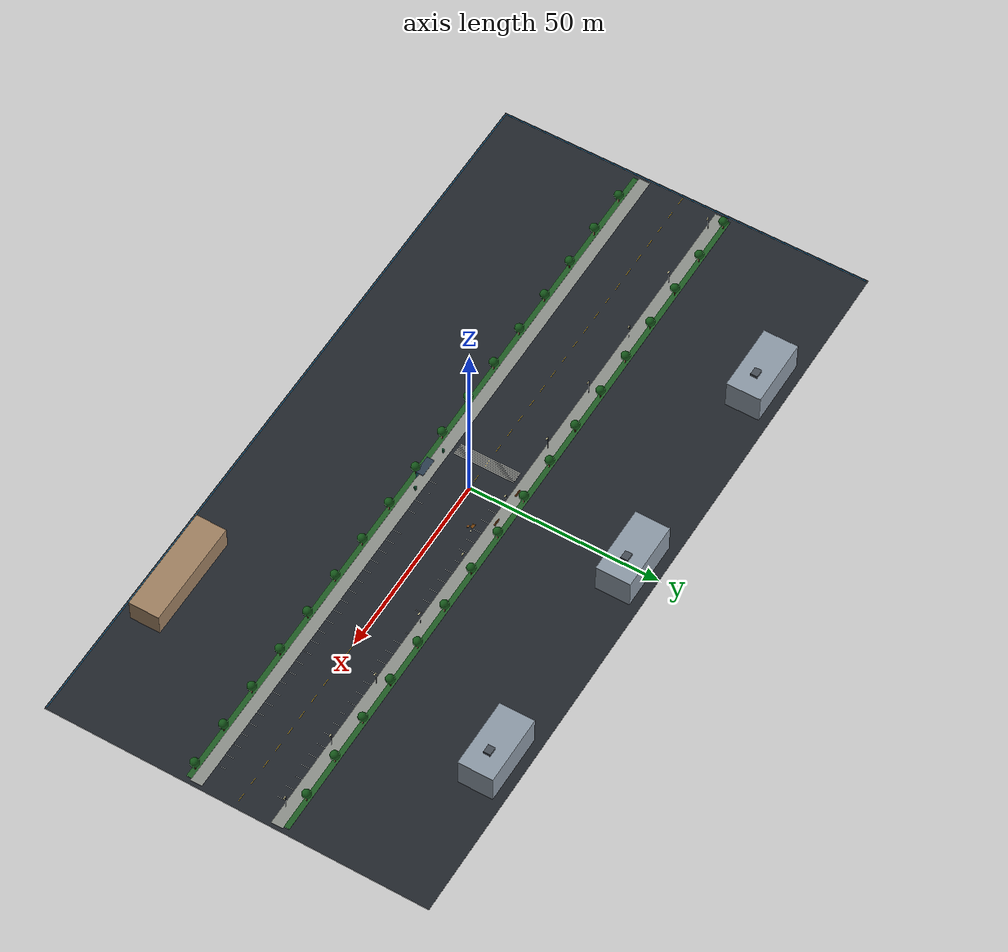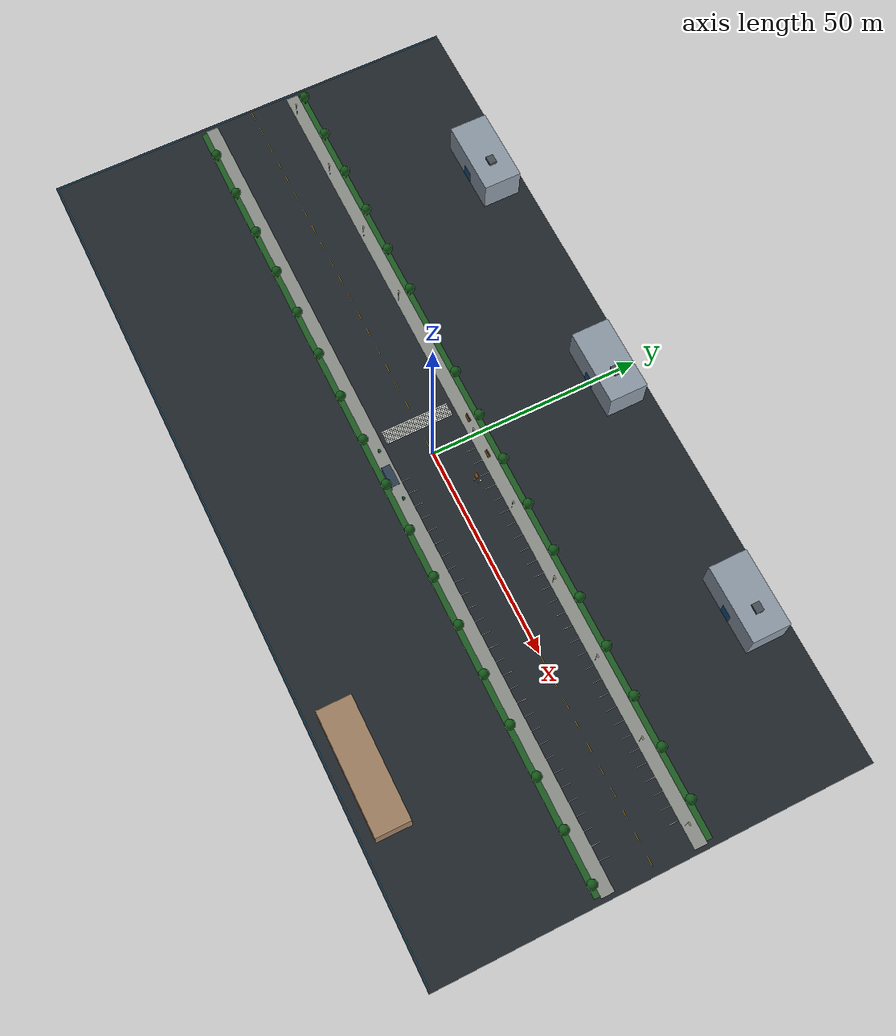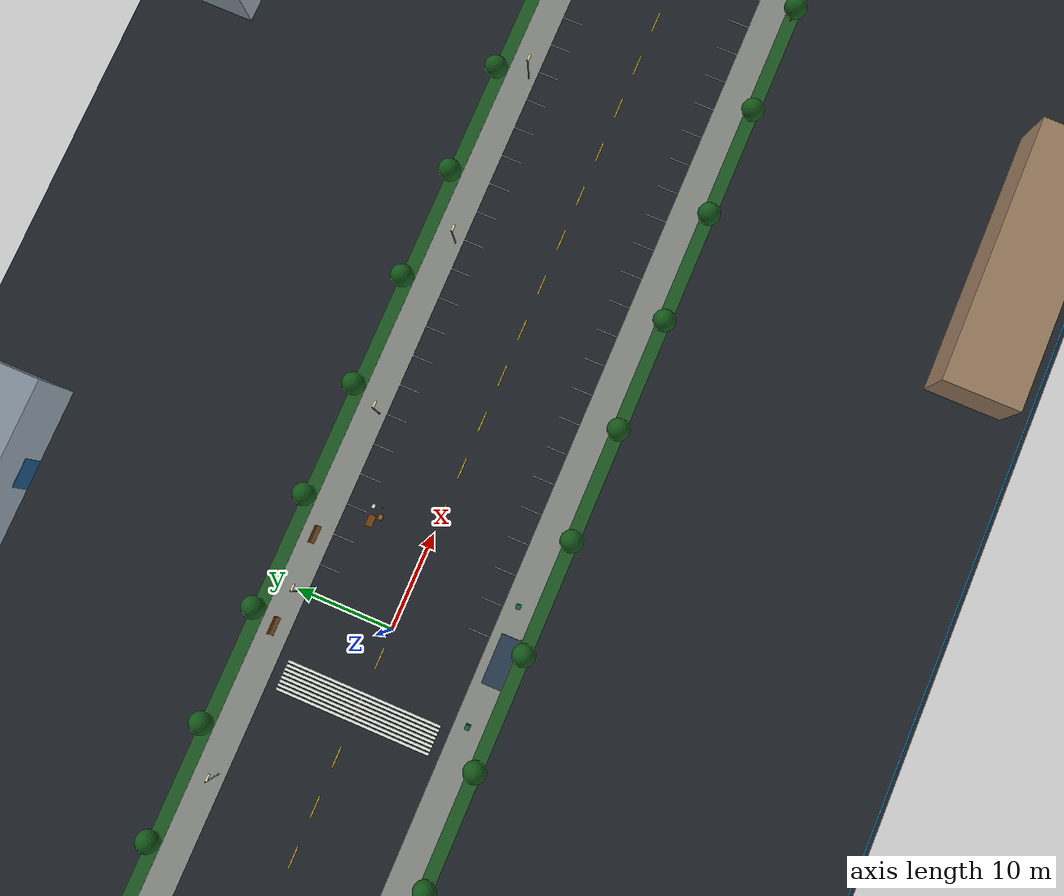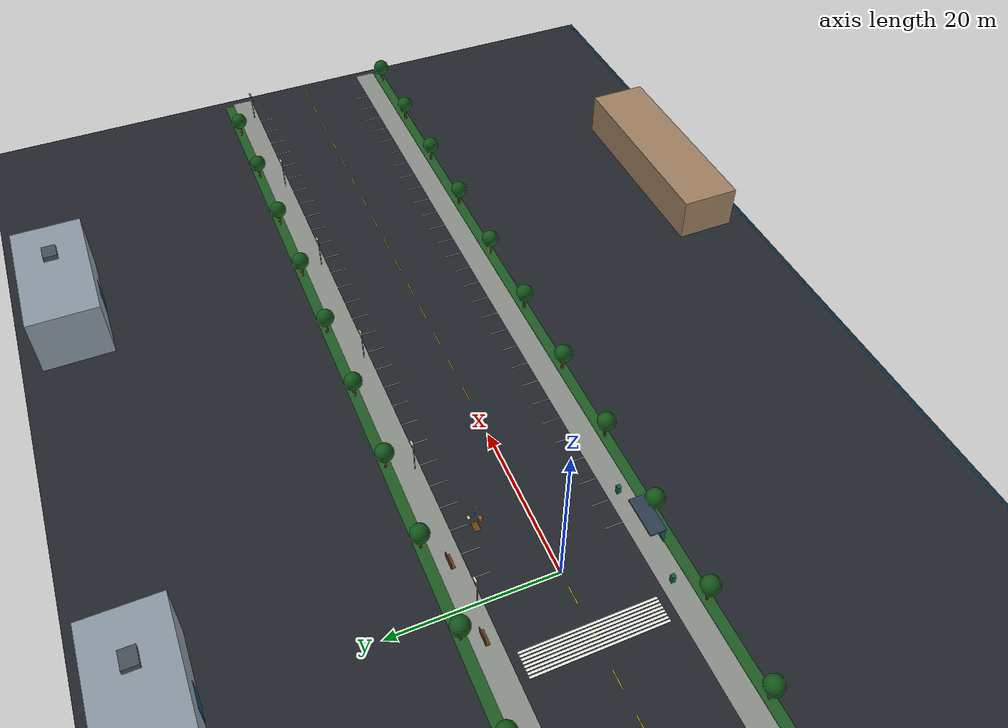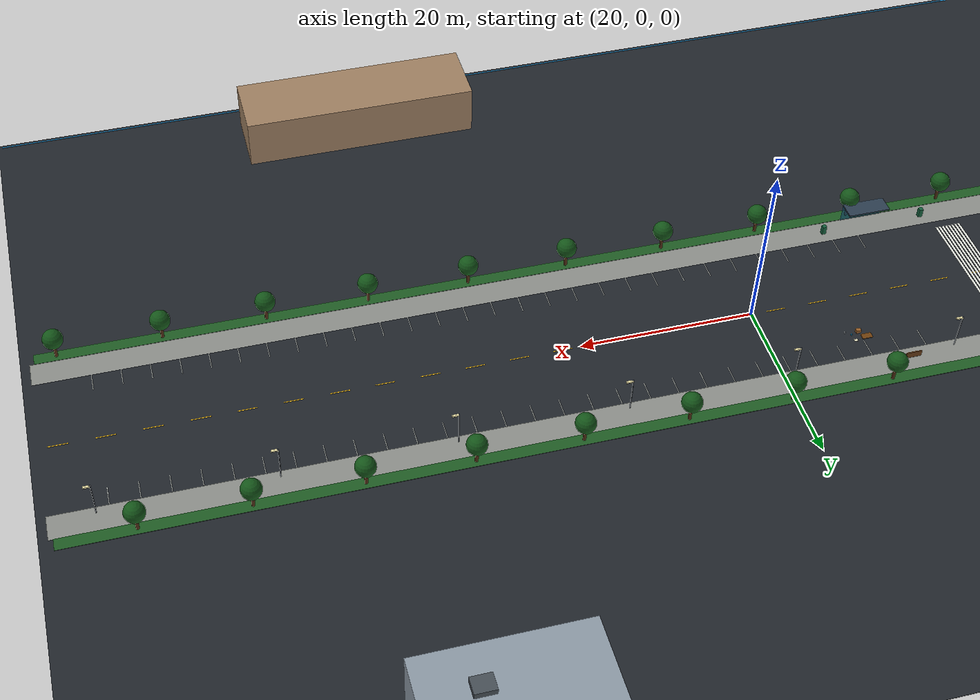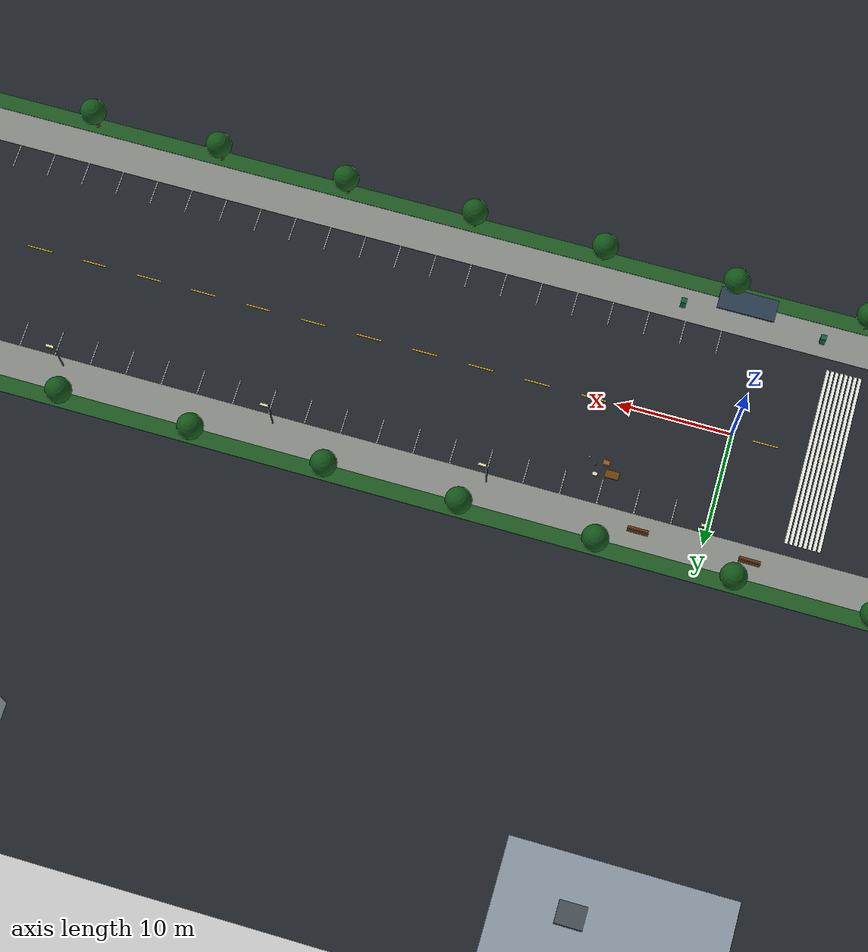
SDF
<?xml version='1.0' encoding='utf-8'?>
<sdf version="1.9">
  <world name="sanitation_campus_large">
    <plugin filename="gz-sim-physics-system" name="gz::sim::systems::Physics" />
    <plugin filename="gz-sim-user-commands-system" name="gz::sim::systems::UserCommands" />
    <plugin filename="gz-sim-scene-broadcaster-system" name="gz::sim::systems::SceneBroadcaster" />
    <plugin filename="gz-sim-sensors-system" name="gz::sim::systems::Sensors">
      <render_engine>ogre2</render_engine>
    </plugin>
    <plugin filename="gz-sim-navsat-system" name="gz::sim::systems::NavSat" />
    <spherical_coordinates>
      <surface_model>EARTH_WGS84</surface_model>
      <world_frame_orientation>ENU</world_frame_orientation>
      <latitude_deg>31.2304</latitude_deg>
      <longitude_deg>121.4737</longitude_deg>
      <elevation>0</elevation>
      <heading_deg>0</heading_deg>
    </spherical_coordinates>
    <gravity>0 0 -9.81</gravity>
    <physics name="1ms" type="ignored">
      <max_step_size>0.005</max_step_size>
      <real_time_factor>1.0</real_time_factor>
    </physics>
    <scene>
      <ambient>0.58 0.60 0.62 1</ambient>
      <background>0.72 0.84 0.94 1</background>
      <shadows>true</shadows>
    </scene>
    <light type="directional" name="sun">
      <cast_shadows>true</cast_shadows>
      <pose>0 0 80 0 0 0</pose>
      <diffuse>0.96 0.91 0.82 1</diffuse>
      <direction>-0.45 0.25 -1.0</direction>
    </light>
    <model name="asphalt_ground">
      <static>true</static>
      <pose>0 0 -0.05 0 0 0</pose>
      <link name="link">
        <collision name="collision">
          <geometry>
            <box>
              <size>200.0 100.0 0.1</size>
            </box>
          </geometry>
        </collision>
        <visual name="visual">
          <geometry>
            <box>
              <size>200.0 100.0 0.1</size>
            </box>
          </geometry>
          <material>
            <ambient>0.13 0.15 0.17 1</ambient>
            <diffuse>0.13 0.15 0.17 1</diffuse>
            <specular>0.04 0.04 0.04 1</specular>
          </material>
        </visual>
      </link>
    </model>
    <model name="north_sidewalk">
      <static>true</static>
      <pose>0 10.5 0.001 0 0 0</pose>
      <link name="link">
        <visual name="visual">
          <geometry>
            <box>
              <size>198.0 3.0 0.002</size>
            </box>
          </geometry>
          <material>
            <ambient>0.55 0.56 0.54 1</ambient>
            <diffuse>0.55 0.56 0.54 1</diffuse>
            <specular>0.04 0.04 0.04 1</specular>
          </material>
        </visual>
      </link>
    </model>
    <model name="south_sidewalk">
      <static>true</static>
      <pose>0 -10.5 0.001 0 0 0</pose>
      <link name="link">
        <visual name="visual">
          <geometry>
            <box>
              <size>198.0 3.0 0.002</size>
            </box>
          </geometry>
          <material>
            <ambient>0.55 0.56 0.54 1</ambient>
            <diffuse>0.55 0.56 0.54 1</diffuse>
            <specular>0.04 0.04 0.04 1</specular>
          </material>
        </visual>
      </link>
    </model>
    <model name="north_green_verge">
      <static>true</static>
      <pose>0 12.7 0.03 0 0 0</pose>
      <link name="link">
        <visual name="visual">
          <geometry>
            <box>
              <size>197.0 1.4 0.06</size>
            </box>
          </geometry>
          <material>
            <ambient>0.12 0.36 0.14 1</ambient>
            <diffuse>0.12 0.36 0.14 1</diffuse>
            <specular>0.04 0.04 0.04 1</specular>
          </material>
        </visual>
      </link>
    </model>
    <model name="south_green_verge">
      <static>true</static>
      <pose>0 -12.7 0.03 0 0 0</pose>
      <link name="link">
        <visual name="visual">
          <geometry>
            <box>
              <size>197.0 1.4 0.06</size>
            </box>
          </geometry>
          <material>
            <ambient>0.12 0.36 0.14 1</ambient>
            <diffuse>0.12 0.36 0.14 1</diffuse>
            <specular>0.04 0.04 0.04 1</specular>
          </material>
        </visual>
      </link>
    </model>
    <model name="center_dash_00">
      <static>true</static>
      <pose>-98.0 0 0.012 0 0 0</pose>
      <link name="link">
        <visual name="visual">
          <geometry>
            <box>
              <size>2.2 0.12 0.012</size>
            </box>
          </geometry>
          <material>
            <ambient>0.95 0.74 0.10 1</ambient>
            <diffuse>0.95 0.74 0.10 1</diffuse>
            <specular>0.04 0.04 0.04 1</specular>
          </material>
        </visual>
      </link>
    </model>
    <model name="center_dash_01">
      <static>true</static>
      <pose>-93.0 0 0.012 0 0 0</pose>
      <link name="link">
        <visual name="visual">
          <geometry>
            <box>
              <size>2.2 0.12 0.012</size>
            </box>
          </geometry>
          <material>
            <ambient>0.95 0.74 0.10 1</ambient>
            <diffuse>0.95 0.74 0.10 1</diffuse>
            <specular>0.04 0.04 0.04 1</specular>
          </material>
        </visual>
      </link>
    </model>
    <model name="center_dash_02">
      <static>true</static>
      <pose>-88.0 0 0.012 0 0 0</pose>
      <link name="link">
        <visual name="visual">
          <geometry>
            <box>
              <size>2.2 0.12 0.012</size>
            </box>
          </geometry>
          <material>
            <ambient>0.95 0.74 0.10 1</ambient>
            <diffuse>0.95 0.74 0.10 1</diffuse>
            <specular>0.04 0.04 0.04 1</specular>
          </material>
        </visual>
      </link>
    </model>
    <model name="center_dash_03">
      <static>true</static>
      <pose>-83.0 0 0.012 0 0 0</pose>
      <link name="link">
        <visual name="visual">
          <geometry>
            <box>
              <size>2.2 0.12 0.012</size>
            </box>
          </geometry>
          <material>
            <ambient>0.95 0.74 0.10 1</ambient>
            <diffuse>0.95 0.74 0.10 1</diffuse>
            <specular>0.04 0.04 0.04 1</specular>
          </material>
        </visual>
      </link>
    </model>
    <model name="center_dash_04">
      <static>true</static>
      <pose>-78.0 0 0.012 0 0 0</pose>
      <link name="link">
        <visual name="visual">
          <geometry>
            <box>
              <size>2.2 0.12 0.012</size>
            </box>
          </geometry>
          <material>
            <ambient>0.95 0.74 0.10 1</ambient>
            <diffuse>0.95 0.74 0.10 1</diffuse>
            <specular>0.04 0.04 0.04 1</specular>
          </material>
        </visual>
      </link>
    </model>
    <model name="center_dash_05">
      <static>true</static>
      <pose>-73.0 0 0.012 0 0 0</pose>
      <link name="link">
        <visual name="visual">
          <geometry>
            <box>
              <size>2.2 0.12 0.012</size>
            </box>
          </geometry>
          <material>
            <ambient>0.95 0.74 0.10 1</ambient>
            <diffuse>0.95 0.74 0.10 1</diffuse>
            <specular>0.04 0.04 0.04 1</specular>
          </material>
        </visual>
      </link>
    </model>
    <model name="center_dash_06">
      <static>true</static>
      <pose>-68.0 0 0.012 0 0 0</pose>
      <link name="link">
        <visual name="visual">
          <geometry>
            <box>
              <size>2.2 0.12 0.012</size>
            </box>
          </geometry>
          <material>
            <ambient>0.95 0.74 0.10 1</ambient>
            <diffuse>0.95 0.74 0.10 1</diffuse>
            <specular>0.04 0.04 0.04 1</specular>
          </material>
        </visual>
      </link>
    </model>
    <model name="center_dash_07">
      <static>true</static>
      <pose>-63.0 0 0.012 0 0 0</pose>
      <link name="link">
        <visual name="visual">
          <geometry>
            <box>
              <size>2.2 0.12 0.012</size>
            </box>
          </geometry>
          <material>
            <ambient>0.95 0.74 0.10 1</ambient>
            <diffuse>0.95 0.74 0.10 1</diffuse>
            <specular>0.04 0.04 0.04 1</specular>
          </material>
        </visual>
      </link>
    </model>
    <model name="center_dash_08">
      <static>true</static>
      <pose>-58.0 0 0.012 0 0 0</pose>
      <link name="link">
        <visual name="visual">
          <geometry>
            <box>
              <size>2.2 0.12 0.012</size>
            </box>
          </geometry>
          <material>
            <ambient>0.95 0.74 0.10 1</ambient>
            <diffuse>0.95 0.74 0.10 1</diffuse>
            <specular>0.04 0.04 0.04 1</specular>
          </material>
        </visual>
      </link>
    </model>
    <model name="center_dash_09">
      <static>true</static>
      <pose>-53.0 0 0.012 0 0 0</pose>
      <link name="link">
        <visual name="visual">
          <geometry>
            <box>
              <size>2.2 0.12 0.012</size>
            </box>
          </geometry>
          <material>
            <ambient>0.95 0.74 0.10 1</ambient>
            <diffuse>0.95 0.74 0.10 1</diffuse>
            <specular>0.04 0.04 0.04 1</specular>
          </material>
        </visual>
      </link>
    </model>
    <model name="center_dash_10">
      <static>true</static>
      <pose>-48.0 0 0.012 0 0 0</pose>
      <link name="link">
        <visual name="visual">
          <geometry>
            <box>
              <size>2.2 0.12 0.012</size>
            </box>
          </geometry>
          <material>
            <ambient>0.95 0.74 0.10 1</ambient>
            <diffuse>0.95 0.74 0.10 1</diffuse>
            <specular>0.04 0.04 0.04 1</specular>
          </material>
        </visual>
      </link>
    </model>
    <model name="center_dash_11">
      <static>true</static>
      <pose>-43.0 0 0.012 0 0 0</pose>
      <link name="link">
        <visual name="visual">
          <geometry>
            <box>
              <size>2.2 0.12 0.012</size>
            </box>
          </geometry>
          <material>
            <ambient>0.95 0.74 0.10 1</ambient>
            <diffuse>0.95 0.74 0.10 1</diffuse>
            <specular>0.04 0.04 0.04 1</specular>
          </material>
        </visual>
      </link>
    </model>
    <model name="center_dash_12">
      <static>true</static>
      <pose>-38.0 0 0.012 0 0 0</pose>
      <link name="link">
        <visual name="visual">
          <geometry>
            <box>
              <size>2.2 0.12 0.012</size>
            </box>
          </geometry>
          <material>
            <ambient>0.95 0.74 0.10 1</ambient>
            <diffuse>0.95 0.74 0.10 1</diffuse>
            <specular>0.04 0.04 0.04 1</specular>
          </material>
        </visual>
      </link>
    </model>
    <model name="center_dash_13">
      <static>true</static>
      <pose>-33.0 0 0.012 0 0 0</pose>
      <link name="link">
        <visual name="visual">
          <geometry>
            <box>
              <size>2.2 0.12 0.012</size>
            </box>
          </geometry>
          <material>
            <ambient>0.95 0.74 0.10 1</ambient>
            <diffuse>0.95 0.74 0.10 1</diffuse>
            <specular>0.04 0.04 0.04 1</specular>
          </material>
        </visual>
      </link>
    </model>
    <model name="center_dash_14">
      <static>true</static>
      <pose>-28.0 0 0.012 0 0 0</pose>
      <link name="link">
        <visual name="visual">
          <geometry>
            <box>
              <size>2.2 0.12 0.012</size>
            </box>
          </geometry>
          <material>
            <ambient>0.95 0.74 0.10 1</ambient>
            <diffuse>0.95 0.74 0.10 1</diffuse>
            <specular>0.04 0.04 0.04 1</specular>
          </material>
        </visual>
      </link>
    </model>
    <model name="center_dash_15">
      <static>true</static>
      <pose>-23.0 0 0.012 0 0 0</pose>
      <link name="link">
        <visual name="visual">
          <geometry>
            <box>
              <size>2.2 0.12 0.012</size>
            </box>
          </geometry>
          <material>
            <ambient>0.95 0.74 0.10 1</ambient>
            <diffuse>0.95 0.74 0.10 1</diffuse>
            <specular>0.04 0.04 0.04 1</specular>
          </material>
        </visual>
      </link>
    </model>
    <model name="center_dash_16">
      <static>true</static>
      <pose>-18.0 0 0.012 0 0 0</pose>
      <link name="link">
        <visual name="visual">
          <geometry>
            <box>
              <size>2.2 0.12 0.012</size>
            </box>
          </geometry>
          <material>
            <ambient>0.95 0.74 0.10 1</ambient>
            <diffuse>0.95 0.74 0.10 1</diffuse>
            <specular>0.04 0.04 0.04 1</specular>
          </material>
        </visual>
      </link>
    </model>
    <model name="center_dash_17">
      <static>true</static>
      <pose>-13.0 0 0.012 0 0 0</pose>
      <link name="link">
        <visual name="visual">
          <geometry>
            <box>
              <size>2.2 0.12 0.012</size>
            </box>
          </geometry>
          <material>
            <ambient>0.95 0.74 0.10 1</ambient>
            <diffuse>0.95 0.74 0.10 1</diffuse>
            <specular>0.04 0.04 0.04 1</specular>
          </material>
        </visual>
      </link>
    </model>
    <model name="center_dash_18">
      <static>true</static>
      <pose>-8.0 0 0.012 0 0 0</pose>
      <link name="link">
        <visual name="visual">
          <geometry>
            <box>
              <size>2.2 0.12 0.012</size>
            </box>
          </geometry>
          <material>
            <ambient>0.95 0.74 0.10 1</ambient>
            <diffuse>0.95 0.74 0.10 1</diffuse>
            <specular>0.04 0.04 0.04 1</specular>
          </material>
        </visual>
      </link>
    </model>
    <model name="center_dash_19">
      <static>true</static>
      <pose>-3.0 0 0.012 0 0 0</pose>
      <link name="link">
        <visual name="visual">
          <geometry>
            <box>
              <size>2.2 0.12 0.012</size>
            </box>
          </geometry>
          <material>
            <ambient>0.95 0.74 0.10 1</ambient>
            <diffuse>0.95 0.74 0.10 1</diffuse>
            <specular>0.04 0.04 0.04 1</specular>
          </material>
        </visual>
      </link>
    </model>
    <model name="center_dash_20">
      <static>true</static>
      <pose>2.0 0 0.012 0 0 0</pose>
      <link name="link">
        <visual name="visual">
          <geometry>
            <box>
              <size>2.2 0.12 0.012</size>
            </box>
          </geometry>
          <material>
            <ambient>0.95 0.74 0.10 1</ambient>
            <diffuse>0.95 0.74 0.10 1</diffuse>
            <specular>0.04 0.04 0.04 1</specular>
          </material>
        </visual>
      </link>
    </model>
    <model name="center_dash_21">
      <static>true</static>
      <pose>7.0 0 0.012 0 0 0</pose>
      <link name="link">
        <visual name="visual">
          <geometry>
            <box>
              <size>2.2 0.12 0.012</size>
            </box>
          </geometry>
          <material>
            <ambient>0.95 0.74 0.10 1</ambient>
            <diffuse>0.95 0.74 0.10 1</diffuse>
            <specular>0.04 0.04 0.04 1</specular>
          </material>
        </visual>
      </link>
    </model>
    <model name="center_dash_22">
      <static>true</static>
      <pose>12.0 0 0.012 0 0 0</pose>
      <link name="link">
        <visual name="visual">
          <geometry>
            <box>
              <size>2.2 0.12 0.012</size>
            </box>
          </geometry>
          <material>
            <ambient>0.95 0.74 0.10 1</ambient>
            <diffuse>0.95 0.74 0.10 1</diffuse>
            <specular>0.04 0.04 0.04 1</specular>
          </material>
        </visual>
      </link>
    </model>
    <model name="center_dash_23">
      <static>true</static>
      <pose>17.0 0 0.012 0 0 0</pose>
      <link name="link">
        <visual name="visual">
          <geometry>
            <box>
              <size>2.2 0.12 0.012</size>
            </box>
          </geometry>
          <material>
            <ambient>0.95 0.74 0.10 1</ambient>
            <diffuse>0.95 0.74 0.10 1</diffuse>
            <specular>0.04 0.04 0.04 1</specular>
          </material>
        </visual>
      </link>
    </model>
    <model name="center_dash_24">
      <static>true</static>
      <pose>22.0 0 0.012 0 0 0</pose>
      <link name="link">
        <visual name="visual">
          <geometry>
            <box>
              <size>2.2 0.12 0.012</size>
            </box>
          </geometry>
          <material>
            <ambient>0.95 0.74 0.10 1</ambient>
            <diffuse>0.95 0.74 0.10 1</diffuse>
            <specular>0.04 0.04 0.04 1</specular>
          </material>
        </visual>
      </link>
    </model>
    <model name="center_dash_25">
      <static>true</static>
      <pose>27.0 0 0.012 0 0 0</pose>
      <link name="link">
        <visual name="visual">
          <geometry>
            <box>
              <size>2.2 0.12 0.012</size>
            </box>
          </geometry>
          <material>
            <ambient>0.95 0.74 0.10 1</ambient>
            <diffuse>0.95 0.74 0.10 1</diffuse>
            <specular>0.04 0.04 0.04 1</specular>
          </material>
        </visual>
      </link>
    </model>
    <model name="center_dash_26">
      <static>true</static>
      <pose>32.0 0 0.012 0 0 0</pose>
      <link name="link">
        <visual name="visual">
          <geometry>
            <box>
              <size>2.2 0.12 0.012</size>
            </box>
          </geometry>
          <material>
            <ambient>0.95 0.74 0.10 1</ambient>
            <diffuse>0.95 0.74 0.10 1</diffuse>
            <specular>0.04 0.04 0.04 1</specular>
          </material>
        </visual>
      </link>
    </model>
    <model name="center_dash_27">
      <static>true</static>
      <pose>37.0 0 0.012 0 0 0</pose>
      <link name="link">
        <visual name="visual">
          <geometry>
            <box>
              <size>2.2 0.12 0.012</size>
            </box>
          </geometry>
          <material>
            <ambient>0.95 0.74 0.10 1</ambient>
            <diffuse>0.95 0.74 0.10 1</diffuse>
            <specular>0.04 0.04 0.04 1</specular>
          </material>
        </visual>
      </link>
    </model>
    <model name="center_dash_28">
      <static>true</static>
      <pose>42.0 0 0.012 0 0 0</pose>
      <link name="link">
        <visual name="visual">
          <geometry>
            <box>
              <size>2.2 0.12 0.012</size>
            </box>
          </geometry>
          <material>
            <ambient>0.95 0.74 0.10 1</ambient>
            <diffuse>0.95 0.74 0.10 1</diffuse>
            <specular>0.04 0.04 0.04 1</specular>
          </material>
        </visual>
      </link>
    </model>
    <model name="center_dash_29">
      <static>true</static>
      <pose>47.0 0 0.012 0 0 0</pose>
      <link name="link">
        <visual name="visual">
          <geometry>
            <box>
              <size>2.2 0.12 0.012</size>
            </box>
          </geometry>
          <material>
            <ambient>0.95 0.74 0.10 1</ambient>
            <diffuse>0.95 0.74 0.10 1</diffuse>
            <specular>0.04 0.04 0.04 1</specular>
          </material>
        </visual>
      </link>
    </model>
    <model name="center_dash_30">
      <static>true</static>
      <pose>52.0 0 0.012 0 0 0</pose>
      <link name="link">
        <visual name="visual">
          <geometry>
            <box>
              <size>2.2 0.12 0.012</size>
            </box>
          </geometry>
          <material>
            <ambient>0.95 0.74 0.10 1</ambient>
            <diffuse>0.95 0.74 0.10 1</diffuse>
            <specular>0.04 0.04 0.04 1</specular>
          </material>
        </visual>
      </link>
    </model>
    <model name="center_dash_31">
      <static>true</static>
      <pose>57.0 0 0.012 0 0 0</pose>
      <link name="link">
        <visual name="visual">
          <geometry>
            <box>
              <size>2.2 0.12 0.012</size>
            </box>
          </geometry>
          <material>
            <ambient>0.95 0.74 0.10 1</ambient>
            <diffuse>0.95 0.74 0.10 1</diffuse>
            <specular>0.04 0.04 0.04 1</specular>
          </material>
        </visual>
      </link>
    </model>
    <model name="center_dash_32">
      <static>true</static>
      <pose>62.0 0 0.012 0 0 0</pose>
      <link name="link">
        <visual name="visual">
          <geometry>
            <box>
              <size>2.2 0.12 0.012</size>
            </box>
          </geometry>
          <material>
            <ambient>0.95 0.74 0.10 1</ambient>
            <diffuse>0.95 0.74 0.10 1</diffuse>
            <specular>0.04 0.04 0.04 1</specular>
          </material>
        </visual>
      </link>
    </model>
    <model name="center_dash_33">
      <static>true</static>
      <pose>67.0 0 0.012 0 0 0</pose>
      <link name="link">
        <visual name="visual">
          <geometry>
            <box>
              <size>2.2 0.12 0.012</size>
            </box>
          </geometry>
          <material>
            <ambient>0.95 0.74 0.10 1</ambient>
            <diffuse>0.95 0.74 0.10 1</diffuse>
            <specular>0.04 0.04 0.04 1</specular>
          </material>
        </visual>
      </link>
    </model>
    <model name="center_dash_34">
      <static>true</static>
      <pose>72.0 0 0.012 0 0 0</pose>
      <link name="link">
        <visual name="visual">
          <geometry>
            <box>
              <size>2.2 0.12 0.012</size>
            </box>
          </geometry>
          <material>
            <ambient>0.95 0.74 0.10 1</ambient>
            <diffuse>0.95 0.74 0.10 1</diffuse>
            <specular>0.04 0.04 0.04 1</specular>
          </material>
        </visual>
      </link>
    </model>
    <model name="center_dash_35">
      <static>true</static>
      <pose>77.0 0 0.012 0 0 0</pose>
      <link name="link">
        <visual name="visual">
          <geometry>
            <box>
              <size>2.2 0.12 0.012</size>
            </box>
          </geometry>
          <material>
            <ambient>0.95 0.74 0.10 1</ambient>
            <diffuse>0.95 0.74 0.10 1</diffuse>
            <specular>0.04 0.04 0.04 1</specular>
          </material>
        </visual>
      </link>
    </model>
    <model name="center_dash_36">
      <static>true</static>
      <pose>82.0 0 0.012 0 0 0</pose>
      <link name="link">
        <visual name="visual">
          <geometry>
            <box>
              <size>2.2 0.12 0.012</size>
            </box>
          </geometry>
          <material>
            <ambient>0.95 0.74 0.10 1</ambient>
            <diffuse>0.95 0.74 0.10 1</diffuse>
            <specular>0.04 0.04 0.04 1</specular>
          </material>
        </visual>
      </link>
    </model>
    <model name="center_dash_37">
      <static>true</static>
      <pose>87.0 0 0.012 0 0 0</pose>
      <link name="link">
        <visual name="visual">
          <geometry>
            <box>
              <size>2.2 0.12 0.012</size>
            </box>
          </geometry>
          <material>
            <ambient>0.95 0.74 0.10 1</ambient>
            <diffuse>0.95 0.74 0.10 1</diffuse>
            <specular>0.04 0.04 0.04 1</specular>
          </material>
        </visual>
      </link>
    </model>
    <model name="center_dash_38">
      <static>true</static>
      <pose>92.0 0 0.012 0 0 0</pose>
      <link name="link">
        <visual name="visual">
          <geometry>
            <box>
              <size>2.2 0.12 0.012</size>
            </box>
          </geometry>
          <material>
            <ambient>0.95 0.74 0.10 1</ambient>
            <diffuse>0.95 0.74 0.10 1</diffuse>
            <specular>0.04 0.04 0.04 1</specular>
          </material>
        </visual>
      </link>
    </model>
    <model name="center_dash_39">
      <static>true</static>
      <pose>97.0 0 0.012 0 0 0</pose>
      <link name="link">
        <visual name="visual">
          <geometry>
            <box>
              <size>2.2 0.12 0.012</size>
            </box>
          </geometry>
          <material>
            <ambient>0.95 0.74 0.10 1</ambient>
            <diffuse>0.95 0.74 0.10 1</diffuse>
            <specular>0.04 0.04 0.04 1</specular>
          </material>
        </visual>
      </link>
    </model>
    <model name="crosswalk_00">
      <static>true</static>
      <pose>-9.4 0 0.014 0 0 0</pose>
      <link name="link">
        <visual name="visual">
          <geometry>
            <box>
              <size>0.28 16.0 0.014</size>
            </box>
          </geometry>
          <material>
            <ambient>0.92 0.93 0.90 1</ambient>
            <diffuse>0.92 0.93 0.90 1</diffuse>
            <specular>0.04 0.04 0.04 1</specular>
          </material>
        </visual>
      </link>
    </model>
    <model name="crosswalk_01">
      <static>true</static>
      <pose>-9.0 0 0.014 0 0 0</pose>
      <link name="link">
        <visual name="visual">
          <geometry>
            <box>
              <size>0.28 16.0 0.014</size>
            </box>
          </geometry>
          <material>
            <ambient>0.92 0.93 0.90 1</ambient>
            <diffuse>0.92 0.93 0.90 1</diffuse>
            <specular>0.04 0.04 0.04 1</specular>
          </material>
        </visual>
      </link>
    </model>
    <model name="crosswalk_02">
      <static>true</static>
      <pose>-8.6 0 0.014 0 0 0</pose>
      <link name="link">
        <visual name="visual">
          <geometry>
            <box>
              <size>0.28 16.0 0.014</size>
            </box>
          </geometry>
          <material>
            <ambient>0.92 0.93 0.90 1</ambient>
            <diffuse>0.92 0.93 0.90 1</diffuse>
            <specular>0.04 0.04 0.04 1</specular>
          </material>
        </visual>
      </link>
    </model>
    <model name="crosswalk_03">
      <static>true</static>
      <pose>-8.2 0 0.014 0 0 0</pose>
      <link name="link">
        <visual name="visual">
          <geometry>
            <box>
              <size>0.28 16.0 0.014</size>
            </box>
          </geometry>
          <material>
            <ambient>0.92 0.93 0.90 1</ambient>
            <diffuse>0.92 0.93 0.90 1</diffuse>
            <specular>0.04 0.04 0.04 1</specular>
          </material>
        </visual>
      </link>
    </model>
    <model name="crosswalk_04">
      <static>true</static>
      <pose>-7.8 0 0.014 0 0 0</pose>
      <link name="link">
        <visual name="visual">
          <geometry>
            <box>
              <size>0.28 16.0 0.014</size>
            </box>
          </geometry>
          <material>
            <ambient>0.92 0.93 0.90 1</ambient>
            <diffuse>0.92 0.93 0.90 1</diffuse>
            <specular>0.04 0.04 0.04 1</specular>
          </material>
        </visual>
      </link>
    </model>
    <model name="crosswalk_05">
      <static>true</static>
      <pose>-7.4 0 0.014 0 0 0</pose>
      <link name="link">
        <visual name="visual">
          <geometry>
            <box>
              <size>0.28 16.0 0.014</size>
            </box>
          </geometry>
          <material>
            <ambient>0.92 0.93 0.90 1</ambient>
            <diffuse>0.92 0.93 0.90 1</diffuse>
            <specular>0.04 0.04 0.04 1</specular>
          </material>
        </visual>
      </link>
    </model>
    <model name="crosswalk_06">
      <static>true</static>
      <pose>-7.0 0 0.014 0 0 0</pose>
      <link name="link">
        <visual name="visual">
          <geometry>
            <box>
              <size>0.28 16.0 0.014</size>
            </box>
          </geometry>
          <material>
            <ambient>0.92 0.93 0.90 1</ambient>
            <diffuse>0.92 0.93 0.90 1</diffuse>
            <specular>0.04 0.04 0.04 1</specular>
          </material>
        </visual>
      </link>
    </model>
    <model name="crosswalk_07">
      <static>true</static>
      <pose>-6.6 0 0.014 0 0 0</pose>
      <link name="link">
        <visual name="visual">
          <geometry>
            <box>
              <size>0.28 16.0 0.014</size>
            </box>
          </geometry>
          <material>
            <ambient>0.92 0.93 0.90 1</ambient>
            <diffuse>0.92 0.93 0.90 1</diffuse>
            <specular>0.04 0.04 0.04 1</specular>
          </material>
        </visual>
      </link>
    </model>
    <model name="parking_line_-1_0">
      <static>true</static>
      <pose>3.0 -7.9 0.013 0 0 0</pose>
      <link name="link">
        <visual name="visual">
          <geometry>
            <box>
              <size>0.08 2.2 0.012</size>
            </box>
          </geometry>
          <material>
            <ambient>0.86 0.88 0.86 1</ambient>
            <diffuse>0.86 0.88 0.86 1</diffuse>
            <specular>0.04 0.04 0.04 1</specular>
          </material>
        </visual>
      </link>
    </model>
    <model name="parking_line_1_0">
      <static>true</static>
      <pose>3.0 7.9 0.013 0 0 0</pose>
      <link name="link">
        <visual name="visual">
          <geometry>
            <box>
              <size>0.08 2.2 0.012</size>
            </box>
          </geometry>
          <material>
            <ambient>0.86 0.88 0.86 1</ambient>
            <diffuse>0.86 0.88 0.86 1</diffuse>
            <specular>0.04 0.04 0.04 1</specular>
          </material>
        </visual>
      </link>
    </model>
    <model name="parking_line_-1_1">
      <static>true</static>
      <pose>6.2 -7.9 0.013 0 0 0</pose>
      <link name="link">
        <visual name="visual">
          <geometry>
            <box>
              <size>0.08 2.2 0.012</size>
            </box>
          </geometry>
          <material>
            <ambient>0.86 0.88 0.86 1</ambient>
            <diffuse>0.86 0.88 0.86 1</diffuse>
            <specular>0.04 0.04 0.04 1</specular>
          </material>
        </visual>
      </link>
    </model>
    <model name="parking_line_1_1">
      <static>true</static>
      <pose>6.2 7.9 0.013 0 0 0</pose>
      <link name="link">
        <visual name="visual">
          <geometry>
            <box>
              <size>0.08 2.2 0.012</size>
            </box>
          </geometry>
          <material>
            <ambient>0.86 0.88 0.86 1</ambient>
            <diffuse>0.86 0.88 0.86 1</diffuse>
            <specular>0.04 0.04 0.04 1</specular>
          </material>
        </visual>
      </link>
    </model>
    <model name="parking_line_-1_2">
      <static>true</static>
      <pose>9.4 -7.9 0.013 0 0 0</pose>
      <link name="link">
        <visual name="visual">
          <geometry>
            <box>
              <size>0.08 2.2 0.012</size>
            </box>
          </geometry>
          <material>
            <ambient>0.86 0.88 0.86 1</ambient>
            <diffuse>0.86 0.88 0.86 1</diffuse>
            <specular>0.04 0.04 0.04 1</specular>
          </material>
        </visual>
      </link>
    </model>
    <model name="parking_line_1_2">
      <static>true</static>
      <pose>9.4 7.9 0.013 0 0 0</pose>
      <link name="link">
        <visual name="visual">
          <geometry>
            <box>
              <size>0.08 2.2 0.012</size>
            </box>
          </geometry>
          <material>
            <ambient>0.86 0.88 0.86 1</ambient>
            <diffuse>0.86 0.88 0.86 1</diffuse>
            <specular>0.04 0.04 0.04 1</specular>
          </material>
        </visual>
      </link>
    </model>
    <model name="parking_line_-1_3">
      <static>true</static>
      <pose>12.600000000000001 -7.9 0.013 0 0 0</pose>
      <link name="link">
        <visual name="visual">
          <geometry>
            <box>
              <size>0.08 2.2 0.012</size>
            </box>
          </geometry>
          <material>
            <ambient>0.86 0.88 0.86 1</ambient>
            <diffuse>0.86 0.88 0.86 1</diffuse>
            <specular>0.04 0.04 0.04 1</specular>
          </material>
        </visual>
      </link>
    </model>
    <model name="parking_line_1_3">
      <static>true</static>
      <pose>12.600000000000001 7.9 0.013 0 0 0</pose>
      <link name="link">
        <visual name="visual">
          <geometry>
            <box>
              <size>0.08 2.2 0.012</size>
            </box>
          </geometry>
          <material>
            <ambient>0.86 0.88 0.86 1</ambient>
            <diffuse>0.86 0.88 0.86 1</diffuse>
            <specular>0.04 0.04 0.04 1</specular>
          </material>
        </visual>
      </link>
    </model>
    <model name="parking_line_-1_4">
      <static>true</static>
      <pose>15.8 -7.9 0.013 0 0 0</pose>
      <link name="link">
        <visual name="visual">
          <geometry>
            <box>
              <size>0.08 2.2 0.012</size>
            </box>
          </geometry>
          <material>
            <ambient>0.86 0.88 0.86 1</ambient>
            <diffuse>0.86 0.88 0.86 1</diffuse>
            <specular>0.04 0.04 0.04 1</specular>
          </material>
        </visual>
      </link>
    </model>
    <model name="parking_line_1_4">
      <static>true</static>
      <pose>15.8 7.9 0.013 0 0 0</pose>
      <link name="link">
        <visual name="visual">
          <geometry>
            <box>
              <size>0.08 2.2 0.012</size>
            </box>
          </geometry>
          <material>
            <ambient>0.86 0.88 0.86 1</ambient>
            <diffuse>0.86 0.88 0.86 1</diffuse>
            <specular>0.04 0.04 0.04 1</specular>
          </material>
        </visual>
      </link>
    </model>
    <model name="parking_line_-1_5">
      <static>true</static>
      <pose>19.0 -7.9 0.013 0 0 0</pose>
      <link name="link">
        <visual name="visual">
          <geometry>
            <box>
              <size>0.08 2.2 0.012</size>
            </box>
          </geometry>
          <material>
            <ambient>0.86 0.88 0.86 1</ambient>
            <diffuse>0.86 0.88 0.86 1</diffuse>
            <specular>0.04 0.04 0.04 1</specular>
          </material>
        </visual>
      </link>
    </model>
    <model name="parking_line_1_5">
      <static>true</static>
      <pose>19.0 7.9 0.013 0 0 0</pose>
      <link name="link">
        <visual name="visual">
          <geometry>
            <box>
              <size>0.08 2.2 0.012</size>
            </box>
          </geometry>
          <material>
            <ambient>0.86 0.88 0.86 1</ambient>
            <diffuse>0.86 0.88 0.86 1</diffuse>
            <specular>0.04 0.04 0.04 1</specular>
          </material>
        </visual>
      </link>
    </model>
    <model name="parking_line_-1_6">
      <static>true</static>
      <pose>22.200000000000003 -7.9 0.013 0 0 0</pose>
      <link name="link">
        <visual name="visual">
          <geometry>
            <box>
              <size>0.08 2.2 0.012</size>
            </box>
          </geometry>
          <material>
            <ambient>0.86 0.88 0.86 1</ambient>
            <diffuse>0.86 0.88 0.86 1</diffuse>
            <specular>0.04 0.04 0.04 1</specular>
          </material>
        </visual>
      </link>
    </model>
    <model name="parking_line_1_6">
      <static>true</static>
      <pose>22.200000000000003 7.9 0.013 0 0 0</pose>
      <link name="link">
        <visual name="visual">
          <geometry>
            <box>
              <size>0.08 2.2 0.012</size>
            </box>
          </geometry>
          <material>
            <ambient>0.86 0.88 0.86 1</ambient>
            <diffuse>0.86 0.88 0.86 1</diffuse>
            <specular>0.04 0.04 0.04 1</specular>
          </material>
        </visual>
      </link>
    </model>
    <model name="parking_line_-1_7">
      <static>true</static>
      <pose>25.400000000000002 -7.9 0.013 0 0 0</pose>
      <link name="link">
        <visual name="visual">
          <geometry>
            <box>
              <size>0.08 2.2 0.012</size>
            </box>
          </geometry>
          <material>
            <ambient>0.86 0.88 0.86 1</ambient>
            <diffuse>0.86 0.88 0.86 1</diffuse>
            <specular>0.04 0.04 0.04 1</specular>
          </material>
        </visual>
      </link>
    </model>
    <model name="parking_line_1_7">
      <static>true</static>
      <pose>25.400000000000002 7.9 0.013 0 0 0</pose>
      <link name="link">
        <visual name="visual">
          <geometry>
            <box>
              <size>0.08 2.2 0.012</size>
            </box>
          </geometry>
          <material>
            <ambient>0.86 0.88 0.86 1</ambient>
            <diffuse>0.86 0.88 0.86 1</diffuse>
            <specular>0.04 0.04 0.04 1</specular>
          </material>
        </visual>
      </link>
    </model>
    <model name="parking_line_-1_8">
      <static>true</static>
      <pose>28.6 -7.9 0.013 0 0 0</pose>
      <link name="link">
        <visual name="visual">
          <geometry>
            <box>
              <size>0.08 2.2 0.012</size>
            </box>
          </geometry>
          <material>
            <ambient>0.86 0.88 0.86 1</ambient>
            <diffuse>0.86 0.88 0.86 1</diffuse>
            <specular>0.04 0.04 0.04 1</specular>
          </material>
        </visual>
      </link>
    </model>
    <model name="parking_line_1_8">
      <static>true</static>
      <pose>28.6 7.9 0.013 0 0 0</pose>
      <link name="link">
        <visual name="visual">
          <geometry>
            <box>
              <size>0.08 2.2 0.012</size>
            </box>
          </geometry>
          <material>
            <ambient>0.86 0.88 0.86 1</ambient>
            <diffuse>0.86 0.88 0.86 1</diffuse>
            <specular>0.04 0.04 0.04 1</specular>
          </material>
        </visual>
      </link>
    </model>
    <model name="parking_line_-1_9">
      <static>true</static>
      <pose>31.8 -7.9 0.013 0 0 0</pose>
      <link name="link">
        <visual name="visual">
          <geometry>
            <box>
              <size>0.08 2.2 0.012</size>
            </box>
          </geometry>
          <material>
            <ambient>0.86 0.88 0.86 1</ambient>
            <diffuse>0.86 0.88 0.86 1</diffuse>
            <specular>0.04 0.04 0.04 1</specular>
          </material>
        </visual>
      </link>
    </model>
    <model name="parking_line_1_9">
      <static>true</static>
      <pose>31.8 7.9 0.013 0 0 0</pose>
      <link name="link">
        <visual name="visual">
          <geometry>
            <box>
              <size>0.08 2.2 0.012</size>
            </box>
          </geometry>
          <material>
            <ambient>0.86 0.88 0.86 1</ambient>
            <diffuse>0.86 0.88 0.86 1</diffuse>
            <specular>0.04 0.04 0.04 1</specular>
          </material>
        </visual>
      </link>
    </model>
    <model name="parking_line_-1_10">
      <static>true</static>
      <pose>35.0 -7.9 0.013 0 0 0</pose>
      <link name="link">
        <visual name="visual">
          <geometry>
            <box>
              <size>0.08 2.2 0.012</size>
            </box>
          </geometry>
          <material>
            <ambient>0.86 0.88 0.86 1</ambient>
            <diffuse>0.86 0.88 0.86 1</diffuse>
            <specular>0.04 0.04 0.04 1</specular>
          </material>
        </visual>
      </link>
    </model>
    <model name="parking_line_1_10">
      <static>true</static>
      <pose>35.0 7.9 0.013 0 0 0</pose>
      <link name="link">
        <visual name="visual">
          <geometry>
            <box>
              <size>0.08 2.2 0.012</size>
            </box>
          </geometry>
          <material>
            <ambient>0.86 0.88 0.86 1</ambient>
            <diffuse>0.86 0.88 0.86 1</diffuse>
            <specular>0.04 0.04 0.04 1</specular>
          </material>
        </visual>
      </link>
    </model>
    <model name="parking_line_-1_11">
      <static>true</static>
      <pose>38.2 -7.9 0.013 0 0 0</pose>
      <link name="link">
        <visual name="visual">
          <geometry>
            <box>
              <size>0.08 2.2 0.012</size>
            </box>
          </geometry>
          <material>
            <ambient>0.86 0.88 0.86 1</ambient>
            <diffuse>0.86 0.88 0.86 1</diffuse>
            <specular>0.04 0.04 0.04 1</specular>
          </material>
        </visual>
      </link>
    </model>
    <model name="parking_line_1_11">
      <static>true</static>
      <pose>38.2 7.9 0.013 0 0 0</pose>
      <link name="link">
        <visual name="visual">
          <geometry>
            <box>
              <size>0.08 2.2 0.012</size>
            </box>
          </geometry>
          <material>
            <ambient>0.86 0.88 0.86 1</ambient>
            <diffuse>0.86 0.88 0.86 1</diffuse>
            <specular>0.04 0.04 0.04 1</specular>
          </material>
        </visual>
      </link>
    </model>
    <model name="parking_line_-1_12">
      <static>true</static>
      <pose>41.400000000000006 -7.9 0.013 0 0 0</pose>
      <link name="link">
        <visual name="visual">
          <geometry>
            <box>
              <size>0.08 2.2 0.012</size>
            </box>
          </geometry>
          <material>
            <ambient>0.86 0.88 0.86 1</ambient>
            <diffuse>0.86 0.88 0.86 1</diffuse>
            <specular>0.04 0.04 0.04 1</specular>
          </material>
        </visual>
      </link>
    </model>
    <model name="parking_line_1_12">
      <static>true</static>
      <pose>41.400000000000006 7.9 0.013 0 0 0</pose>
      <link name="link">
        <visual name="visual">
          <geometry>
            <box>
              <size>0.08 2.2 0.012</size>
            </box>
          </geometry>
          <material>
            <ambient>0.86 0.88 0.86 1</ambient>
            <diffuse>0.86 0.88 0.86 1</diffuse>
            <specular>0.04 0.04 0.04 1</specular>
          </material>
        </visual>
      </link>
    </model>
    <model name="parking_line_-1_13">
      <static>true</static>
      <pose>44.6 -7.9 0.013 0 0 0</pose>
      <link name="link">
        <visual name="visual">
          <geometry>
            <box>
              <size>0.08 2.2 0.012</size>
            </box>
          </geometry>
          <material>
            <ambient>0.86 0.88 0.86 1</ambient>
            <diffuse>0.86 0.88 0.86 1</diffuse>
            <specular>0.04 0.04 0.04 1</specular>
          </material>
        </visual>
      </link>
    </model>
    <model name="parking_line_1_13">
      <static>true</static>
      <pose>44.6 7.9 0.013 0 0 0</pose>
      <link name="link">
        <visual name="visual">
          <geometry>
            <box>
              <size>0.08 2.2 0.012</size>
            </box>
          </geometry>
          <material>
            <ambient>0.86 0.88 0.86 1</ambient>
            <diffuse>0.86 0.88 0.86 1</diffuse>
            <specular>0.04 0.04 0.04 1</specular>
          </material>
        </visual>
      </link>
    </model>
    <model name="parking_line_-1_14">
      <static>true</static>
      <pose>47.800000000000004 -7.9 0.013 0 0 0</pose>
      <link name="link">
        <visual name="visual">
          <geometry>
            <box>
              <size>0.08 2.2 0.012</size>
            </box>
          </geometry>
          <material>
            <ambient>0.86 0.88 0.86 1</ambient>
            <diffuse>0.86 0.88 0.86 1</diffuse>
            <specular>0.04 0.04 0.04 1</specular>
          </material>
        </visual>
      </link>
    </model>
    <model name="parking_line_1_14">
      <static>true</static>
      <pose>47.800000000000004 7.9 0.013 0 0 0</pose>
      <link name="link">
        <visual name="visual">
          <geometry>
            <box>
              <size>0.08 2.2 0.012</size>
            </box>
          </geometry>
          <material>
            <ambient>0.86 0.88 0.86 1</ambient>
            <diffuse>0.86 0.88 0.86 1</diffuse>
            <specular>0.04 0.04 0.04 1</specular>
          </material>
        </visual>
      </link>
    </model>
    <model name="parking_line_-1_15">
      <static>true</static>
      <pose>51.0 -7.9 0.013 0 0 0</pose>
      <link name="link">
        <visual name="visual">
          <geometry>
            <box>
              <size>0.08 2.2 0.012</size>
            </box>
          </geometry>
          <material>
            <ambient>0.86 0.88 0.86 1</ambient>
            <diffuse>0.86 0.88 0.86 1</diffuse>
            <specular>0.04 0.04 0.04 1</specular>
          </material>
        </visual>
      </link>
    </model>
    <model name="parking_line_1_15">
      <static>true</static>
      <pose>51.0 7.9 0.013 0 0 0</pose>
      <link name="link">
        <visual name="visual">
          <geometry>
            <box>
              <size>0.08 2.2 0.012</size>
            </box>
          </geometry>
          <material>
            <ambient>0.86 0.88 0.86 1</ambient>
            <diffuse>0.86 0.88 0.86 1</diffuse>
            <specular>0.04 0.04 0.04 1</specular>
          </material>
        </visual>
      </link>
    </model>
    <model name="parking_line_-1_16">
      <static>true</static>
      <pose>54.2 -7.9 0.013 0 0 0</pose>
      <link name="link">
        <visual name="visual">
          <geometry>
            <box>
              <size>0.08 2.2 0.012</size>
            </box>
          </geometry>
          <material>
            <ambient>0.86 0.88 0.86 1</ambient>
            <diffuse>0.86 0.88 0.86 1</diffuse>
            <specular>0.04 0.04 0.04 1</specular>
          </material>
        </visual>
      </link>
    </model>
    <model name="parking_line_1_16">
      <static>true</static>
      <pose>54.2 7.9 0.013 0 0 0</pose>
      <link name="link">
        <visual name="visual">
          <geometry>
            <box>
              <size>0.08 2.2 0.012</size>
            </box>
          </geometry>
          <material>
            <ambient>0.86 0.88 0.86 1</ambient>
            <diffuse>0.86 0.88 0.86 1</diffuse>
            <specular>0.04 0.04 0.04 1</specular>
          </material>
        </visual>
      </link>
    </model>
    <model name="parking_line_-1_17">
      <static>true</static>
      <pose>57.400000000000006 -7.9 0.013 0 0 0</pose>
      <link name="link">
        <visual name="visual">
          <geometry>
            <box>
              <size>0.08 2.2 0.012</size>
            </box>
          </geometry>
          <material>
            <ambient>0.86 0.88 0.86 1</ambient>
            <diffuse>0.86 0.88 0.86 1</diffuse>
            <specular>0.04 0.04 0.04 1</specular>
          </material>
        </visual>
      </link>
    </model>
    <model name="parking_line_1_17">
      <static>true</static>
      <pose>57.400000000000006 7.9 0.013 0 0 0</pose>
      <link name="link">
        <visual name="visual">
          <geometry>
            <box>
              <size>0.08 2.2 0.012</size>
            </box>
          </geometry>
          <material>
            <ambient>0.86 0.88 0.86 1</ambient>
            <diffuse>0.86 0.88 0.86 1</diffuse>
            <specular>0.04 0.04 0.04 1</specular>
          </material>
        </visual>
      </link>
    </model>
    <model name="parking_line_-1_18">
      <static>true</static>
      <pose>60.6 -7.9 0.013 0 0 0</pose>
      <link name="link">
        <visual name="visual">
          <geometry>
            <box>
              <size>0.08 2.2 0.012</size>
            </box>
          </geometry>
          <material>
            <ambient>0.86 0.88 0.86 1</ambient>
            <diffuse>0.86 0.88 0.86 1</diffuse>
            <specular>0.04 0.04 0.04 1</specular>
          </material>
        </visual>
      </link>
    </model>
    <model name="parking_line_1_18">
      <static>true</static>
      <pose>60.6 7.9 0.013 0 0 0</pose>
      <link name="link">
        <visual name="visual">
          <geometry>
            <box>
              <size>0.08 2.2 0.012</size>
            </box>
          </geometry>
          <material>
            <ambient>0.86 0.88 0.86 1</ambient>
            <diffuse>0.86 0.88 0.86 1</diffuse>
            <specular>0.04 0.04 0.04 1</specular>
          </material>
        </visual>
      </link>
    </model>
    <model name="parking_line_-1_19">
      <static>true</static>
      <pose>63.800000000000004 -7.9 0.013 0 0 0</pose>
      <link name="link">
        <visual name="visual">
          <geometry>
            <box>
              <size>0.08 2.2 0.012</size>
            </box>
          </geometry>
          <material>
            <ambient>0.86 0.88 0.86 1</ambient>
            <diffuse>0.86 0.88 0.86 1</diffuse>
            <specular>0.04 0.04 0.04 1</specular>
          </material>
        </visual>
      </link>
    </model>
    <model name="parking_line_1_19">
      <static>true</static>
      <pose>63.800000000000004 7.9 0.013 0 0 0</pose>
      <link name="link">
        <visual name="visual">
          <geometry>
            <box>
              <size>0.08 2.2 0.012</size>
            </box>
          </geometry>
          <material>
            <ambient>0.86 0.88 0.86 1</ambient>
            <diffuse>0.86 0.88 0.86 1</diffuse>
            <specular>0.04 0.04 0.04 1</specular>
          </material>
        </visual>
      </link>
    </model>
    <model name="parking_line_-1_20">
      <static>true</static>
      <pose>67.0 -7.9 0.013 0 0 0</pose>
      <link name="link">
        <visual name="visual">
          <geometry>
            <box>
              <size>0.08 2.2 0.012</size>
            </box>
          </geometry>
          <material>
            <ambient>0.86 0.88 0.86 1</ambient>
            <diffuse>0.86 0.88 0.86 1</diffuse>
            <specular>0.04 0.04 0.04 1</specular>
          </material>
        </visual>
      </link>
    </model>
    <model name="parking_line_1_20">
      <static>true</static>
      <pose>67.0 7.9 0.013 0 0 0</pose>
      <link name="link">
        <visual name="visual">
          <geometry>
            <box>
              <size>0.08 2.2 0.012</size>
            </box>
          </geometry>
          <material>
            <ambient>0.86 0.88 0.86 1</ambient>
            <diffuse>0.86 0.88 0.86 1</diffuse>
            <specular>0.04 0.04 0.04 1</specular>
          </material>
        </visual>
      </link>
    </model>
    <model name="parking_line_-1_21">
      <static>true</static>
      <pose>70.2 -7.9 0.013 0 0 0</pose>
      <link name="link">
        <visual name="visual">
          <geometry>
            <box>
              <size>0.08 2.2 0.012</size>
            </box>
          </geometry>
          <material>
            <ambient>0.86 0.88 0.86 1</ambient>
            <diffuse>0.86 0.88 0.86 1</diffuse>
            <specular>0.04 0.04 0.04 1</specular>
          </material>
        </visual>
      </link>
    </model>
    <model name="parking_line_1_21">
      <static>true</static>
      <pose>70.2 7.9 0.013 0 0 0</pose>
      <link name="link">
        <visual name="visual">
          <geometry>
            <box>
              <size>0.08 2.2 0.012</size>
            </box>
          </geometry>
          <material>
            <ambient>0.86 0.88 0.86 1</ambient>
            <diffuse>0.86 0.88 0.86 1</diffuse>
            <specular>0.04 0.04 0.04 1</specular>
          </material>
        </visual>
      </link>
    </model>
    <model name="parking_line_-1_22">
      <static>true</static>
      <pose>73.4 -7.9 0.013 0 0 0</pose>
      <link name="link">
        <visual name="visual">
          <geometry>
            <box>
              <size>0.08 2.2 0.012</size>
            </box>
          </geometry>
          <material>
            <ambient>0.86 0.88 0.86 1</ambient>
            <diffuse>0.86 0.88 0.86 1</diffuse>
            <specular>0.04 0.04 0.04 1</specular>
          </material>
        </visual>
      </link>
    </model>
    <model name="parking_line_1_22">
      <static>true</static>
      <pose>73.4 7.9 0.013 0 0 0</pose>
      <link name="link">
        <visual name="visual">
          <geometry>
            <box>
              <size>0.08 2.2 0.012</size>
            </box>
          </geometry>
          <material>
            <ambient>0.86 0.88 0.86 1</ambient>
            <diffuse>0.86 0.88 0.86 1</diffuse>
            <specular>0.04 0.04 0.04 1</specular>
          </material>
        </visual>
      </link>
    </model>
    <model name="parking_line_-1_23">
      <static>true</static>
      <pose>76.60000000000001 -7.9 0.013 0 0 0</pose>
      <link name="link">
        <visual name="visual">
          <geometry>
            <box>
              <size>0.08 2.2 0.012</size>
            </box>
          </geometry>
          <material>
            <ambient>0.86 0.88 0.86 1</ambient>
            <diffuse>0.86 0.88 0.86 1</diffuse>
            <specular>0.04 0.04 0.04 1</specular>
          </material>
        </visual>
      </link>
    </model>
    <model name="parking_line_1_23">
      <static>true</static>
      <pose>76.60000000000001 7.9 0.013 0 0 0</pose>
      <link name="link">
        <visual name="visual">
          <geometry>
            <box>
              <size>0.08 2.2 0.012</size>
            </box>
          </geometry>
          <material>
            <ambient>0.86 0.88 0.86 1</ambient>
            <diffuse>0.86 0.88 0.86 1</diffuse>
            <specular>0.04 0.04 0.04 1</specular>
          </material>
        </visual>
      </link>
    </model>
    <model name="parking_line_-1_24">
      <static>true</static>
      <pose>79.80000000000001 -7.9 0.013 0 0 0</pose>
      <link name="link">
        <visual name="visual">
          <geometry>
            <box>
              <size>0.08 2.2 0.012</size>
            </box>
          </geometry>
          <material>
            <ambient>0.86 0.88 0.86 1</ambient>
            <diffuse>0.86 0.88 0.86 1</diffuse>
            <specular>0.04 0.04 0.04 1</specular>
          </material>
        </visual>
      </link>
    </model>
    <model name="parking_line_1_24">
      <static>true</static>
      <pose>79.80000000000001 7.9 0.013 0 0 0</pose>
      <link name="link">
        <visual name="visual">
          <geometry>
            <box>
              <size>0.08 2.2 0.012</size>
            </box>
          </geometry>
          <material>
            <ambient>0.86 0.88 0.86 1</ambient>
            <diffuse>0.86 0.88 0.86 1</diffuse>
            <specular>0.04 0.04 0.04 1</specular>
          </material>
        </visual>
      </link>
    </model>
    <model name="parking_line_-1_25">
      <static>true</static>
      <pose>83.0 -7.9 0.013 0 0 0</pose>
      <link name="link">
        <visual name="visual">
          <geometry>
            <box>
              <size>0.08 2.2 0.012</size>
            </box>
          </geometry>
          <material>
            <ambient>0.86 0.88 0.86 1</ambient>
            <diffuse>0.86 0.88 0.86 1</diffuse>
            <specular>0.04 0.04 0.04 1</specular>
          </material>
        </visual>
      </link>
    </model>
    <model name="parking_line_1_25">
      <static>true</static>
      <pose>83.0 7.9 0.013 0 0 0</pose>
      <link name="link">
        <visual name="visual">
          <geometry>
            <box>
              <size>0.08 2.2 0.012</size>
            </box>
          </geometry>
          <material>
            <ambient>0.86 0.88 0.86 1</ambient>
            <diffuse>0.86 0.88 0.86 1</diffuse>
            <specular>0.04 0.04 0.04 1</specular>
          </material>
        </visual>
      </link>
    </model>
    <model name="parking_line_-1_26">
      <static>true</static>
      <pose>86.2 -7.9 0.013 0 0 0</pose>
      <link name="link">
        <visual name="visual">
          <geometry>
            <box>
              <size>0.08 2.2 0.012</size>
            </box>
          </geometry>
          <material>
            <ambient>0.86 0.88 0.86 1</ambient>
            <diffuse>0.86 0.88 0.86 1</diffuse>
            <specular>0.04 0.04 0.04 1</specular>
          </material>
        </visual>
      </link>
    </model>
    <model name="parking_line_1_26">
      <static>true</static>
      <pose>86.2 7.9 0.013 0 0 0</pose>
      <link name="link">
        <visual name="visual">
          <geometry>
            <box>
              <size>0.08 2.2 0.012</size>
            </box>
          </geometry>
          <material>
            <ambient>0.86 0.88 0.86 1</ambient>
            <diffuse>0.86 0.88 0.86 1</diffuse>
            <specular>0.04 0.04 0.04 1</specular>
          </material>
        </visual>
      </link>
    </model>
    <model name="parking_line_-1_27">
      <static>true</static>
      <pose>89.4 -7.9 0.013 0 0 0</pose>
      <link name="link">
        <visual name="visual">
          <geometry>
            <box>
              <size>0.08 2.2 0.012</size>
            </box>
          </geometry>
          <material>
            <ambient>0.86 0.88 0.86 1</ambient>
            <diffuse>0.86 0.88 0.86 1</diffuse>
            <specular>0.04 0.04 0.04 1</specular>
          </material>
        </visual>
      </link>
    </model>
    <model name="parking_line_1_27">
      <static>true</static>
      <pose>89.4 7.9 0.013 0 0 0</pose>
      <link name="link">
        <visual name="visual">
          <geometry>
            <box>
              <size>0.08 2.2 0.012</size>
            </box>
          </geometry>
          <material>
            <ambient>0.86 0.88 0.86 1</ambient>
            <diffuse>0.86 0.88 0.86 1</diffuse>
            <specular>0.04 0.04 0.04 1</specular>
          </material>
        </visual>
      </link>
    </model>
    <model name="parking_line_-1_28">
      <static>true</static>
      <pose>92.60000000000001 -7.9 0.013 0 0 0</pose>
      <link name="link">
        <visual name="visual">
          <geometry>
            <box>
              <size>0.08 2.2 0.012</size>
            </box>
          </geometry>
          <material>
            <ambient>0.86 0.88 0.86 1</ambient>
            <diffuse>0.86 0.88 0.86 1</diffuse>
            <specular>0.04 0.04 0.04 1</specular>
          </material>
        </visual>
      </link>
    </model>
    <model name="parking_line_1_28">
      <static>true</static>
      <pose>92.60000000000001 7.9 0.013 0 0 0</pose>
      <link name="link">
        <visual name="visual">
          <geometry>
            <box>
              <size>0.08 2.2 0.012</size>
            </box>
          </geometry>
          <material>
            <ambient>0.86 0.88 0.86 1</ambient>
            <diffuse>0.86 0.88 0.86 1</diffuse>
            <specular>0.04 0.04 0.04 1</specular>
          </material>
        </visual>
      </link>
    </model>
    <model name="building_north_0">
      <static>true</static>
      <pose>-60.0 43.0 4.0 0 0 0</pose>
      <link name="link">
        <collision name="collision">
          <geometry>
            <box>
              <size>18.0 9.0 8.0</size>
            </box>
          </geometry>
        </collision>
        <visual name="visual">
          <geometry>
            <box>
              <size>18.0 9.0 8.0</size>
            </box>
          </geometry>
          <material>
            <ambient>0.55 0.60 0.65 1</ambient>
            <diffuse>0.55 0.60 0.65 1</diffuse>
            <specular>0.04 0.04 0.04 1</specular>
          </material>
        </visual>
      </link>
    </model>
    <model name="glass_entry_north_0">
      <static>true</static>
      <pose>-60.0 38.49 1.7 0 0 0</pose>
      <link name="link">
        <visual name="visual">
          <geometry>
            <box>
              <size>3.0 0.08 3.2</size>
            </box>
          </geometry>
          <material>
            <ambient>0.08 0.31 0.48 1</ambient>
            <diffuse>0.08 0.31 0.48 1</diffuse>
            <specular>0.04 0.04 0.04 1</specular>
          </material>
        </visual>
      </link>
    </model>
    <model name="roof_unit_north_0">
      <static>true</static>
      <pose>-57.0 43.0 8.35 0 0 0</pose>
      <link name="link">
        <collision name="collision">
          <geometry>
            <box>
              <size>2.2 1.8 0.7</size>
            </box>
          </geometry>
        </collision>
        <visual name="visual">
          <geometry>
            <box>
              <size>2.2 1.8 0.7</size>
            </box>
          </geometry>
          <material>
            <ambient>0.28 0.31 0.34 1</ambient>
            <diffuse>0.28 0.31 0.34 1</diffuse>
            <specular>0.04 0.04 0.04 1</specular>
          </material>
        </visual>
      </link>
    </model>
    <model name="building_north_1">
      <static>true</static>
      <pose>0.0 43.0 4.0 0 0 0</pose>
      <link name="link">
        <collision name="collision">
          <geometry>
            <box>
              <size>18.0 9.0 8.0</size>
            </box>
          </geometry>
        </collision>
        <visual name="visual">
          <geometry>
            <box>
              <size>18.0 9.0 8.0</size>
            </box>
          </geometry>
          <material>
            <ambient>0.55 0.60 0.65 1</ambient>
            <diffuse>0.55 0.60 0.65 1</diffuse>
            <specular>0.04 0.04 0.04 1</specular>
          </material>
        </visual>
      </link>
    </model>
    <model name="glass_entry_north_1">
      <static>true</static>
      <pose>0.0 38.49 1.7 0 0 0</pose>
      <link name="link">
        <visual name="visual">
          <geometry>
            <box>
              <size>3.0 0.08 3.2</size>
            </box>
          </geometry>
          <material>
            <ambient>0.08 0.31 0.48 1</ambient>
            <diffuse>0.08 0.31 0.48 1</diffuse>
            <specular>0.04 0.04 0.04 1</specular>
          </material>
        </visual>
      </link>
    </model>
    <model name="roof_unit_north_1">
      <static>true</static>
      <pose>3.0 43.0 8.35 0 0 0</pose>
      <link name="link">
        <collision name="collision">
          <geometry>
            <box>
              <size>2.2 1.8 0.7</size>
            </box>
          </geometry>
        </collision>
        <visual name="visual">
          <geometry>
            <box>
              <size>2.2 1.8 0.7</size>
            </box>
          </geometry>
          <material>
            <ambient>0.28 0.31 0.34 1</ambient>
            <diffuse>0.28 0.31 0.34 1</diffuse>
            <specular>0.04 0.04 0.04 1</specular>
          </material>
        </visual>
      </link>
    </model>
    <model name="building_north_2">
      <static>true</static>
      <pose>60.0 43.0 4.0 0 0 0</pose>
      <link name="link">
        <collision name="collision">
          <geometry>
            <box>
              <size>18.0 9.0 8.0</size>
            </box>
          </geometry>
        </collision>
        <visual name="visual">
          <geometry>
            <box>
              <size>18.0 9.0 8.0</size>
            </box>
          </geometry>
          <material>
            <ambient>0.55 0.60 0.65 1</ambient>
            <diffuse>0.55 0.60 0.65 1</diffuse>
            <specular>0.04 0.04 0.04 1</specular>
          </material>
        </visual>
      </link>
    </model>
    <model name="glass_entry_north_2">
      <static>true</static>
      <pose>60.0 38.49 1.7 0 0 0</pose>
      <link name="link">
        <visual name="visual">
          <geometry>
            <box>
              <size>3.0 0.08 3.2</size>
            </box>
          </geometry>
          <material>
            <ambient>0.08 0.31 0.48 1</ambient>
            <diffuse>0.08 0.31 0.48 1</diffuse>
            <specular>0.04 0.04 0.04 1</specular>
          </material>
        </visual>
      </link>
    </model>
    <model name="roof_unit_north_2">
      <static>true</static>
      <pose>63.0 43.0 8.35 0 0 0</pose>
      <link name="link">
        <collision name="collision">
          <geometry>
            <box>
              <size>2.2 1.8 0.7</size>
            </box>
          </geometry>
        </collision>
        <visual name="visual">
          <geometry>
            <box>
              <size>2.2 1.8 0.7</size>
            </box>
          </geometry>
          <material>
            <ambient>0.28 0.31 0.34 1</ambient>
            <diffuse>0.28 0.31 0.34 1</diffuse>
            <specular>0.04 0.04 0.04 1</specular>
          </material>
        </visual>
      </link>
    </model>
    <model name="service_building_south">
      <static>true</static>
      <pose>56.00000000000001 -43.0 3.0 0 0 0</pose>
      <link name="link">
        <collision name="collision">
          <geometry>
            <box>
              <size>28.0 8.0 6.0</size>
            </box>
          </geometry>
        </collision>
        <visual name="visual">
          <geometry>
            <box>
              <size>28.0 8.0 6.0</size>
            </box>
          </geometry>
          <material>
            <ambient>0.62 0.50 0.38 1</ambient>
            <diffuse>0.62 0.50 0.38 1</diffuse>
            <specular>0.04 0.04 0.04 1</specular>
          </material>
        </visual>
      </link>
    </model>
    <model name="tree_00">
      <static>true</static>
      <pose>-96.0 12.7 0 0 0 0</pose>
      <link name="link">
        <collision name="trunk_collision">
          <geometry>
            <cylinder>
              <radius>0.18</radius>
              <length>2.2</length>
            </cylinder>
          </geometry>
          <pose>0 0 1.1 0 0 0</pose>
        </collision>
        <visual name="trunk">
          <pose>0 0 1.1 0 0 0</pose>
          <geometry>
            <cylinder>
              <radius>0.18</radius>
              <length>2.2</length>
            </cylinder>
          </geometry>
          <material>
            <ambient>0.30 0.17 0.07 1</ambient>
            <diffuse>0.30 0.17 0.07 1</diffuse>
            <specular>0.04 0.04 0.04 1</specular>
          </material>
        </visual>
        <visual name="crown">
          <pose>0 0 2.7 0 0 0</pose>
          <geometry>
            <sphere>
              <radius>1.15</radius>
            </sphere>
          </geometry>
          <material>
            <ambient>0.08 0.34 0.10 1</ambient>
            <diffuse>0.08 0.34 0.10 1</diffuse>
            <specular>0.04 0.04 0.04 1</specular>
          </material>
        </visual>
      </link>
    </model>
    <model name="tree_01">
      <static>true</static>
      <pose>-90.18181818181819 -12.7 0 0 0 0</pose>
      <link name="link">
        <collision name="trunk_collision">
          <geometry>
            <cylinder>
              <radius>0.18</radius>
              <length>2.2</length>
            </cylinder>
          </geometry>
          <pose>0 0 1.1 0 0 0</pose>
        </collision>
        <visual name="trunk">
          <pose>0 0 1.1 0 0 0</pose>
          <geometry>
            <cylinder>
              <radius>0.18</radius>
              <length>2.2</length>
            </cylinder>
          </geometry>
          <material>
            <ambient>0.30 0.17 0.07 1</ambient>
            <diffuse>0.30 0.17 0.07 1</diffuse>
            <specular>0.04 0.04 0.04 1</specular>
          </material>
        </visual>
        <visual name="crown">
          <pose>0 0 2.7 0 0 0</pose>
          <geometry>
            <sphere>
              <radius>1.15</radius>
            </sphere>
          </geometry>
          <material>
            <ambient>0.08 0.34 0.10 1</ambient>
            <diffuse>0.08 0.34 0.10 1</diffuse>
            <specular>0.04 0.04 0.04 1</specular>
          </material>
        </visual>
      </link>
    </model>
    <model name="tree_02">
      <static>true</static>
      <pose>-84.36363636363636 12.7 0 0 0 0</pose>
      <link name="link">
        <collision name="trunk_collision">
          <geometry>
            <cylinder>
              <radius>0.18</radius>
              <length>2.2</length>
            </cylinder>
          </geometry>
          <pose>0 0 1.1 0 0 0</pose>
        </collision>
        <visual name="trunk">
          <pose>0 0 1.1 0 0 0</pose>
          <geometry>
            <cylinder>
              <radius>0.18</radius>
              <length>2.2</length>
            </cylinder>
          </geometry>
          <material>
            <ambient>0.30 0.17 0.07 1</ambient>
            <diffuse>0.30 0.17 0.07 1</diffuse>
            <specular>0.04 0.04 0.04 1</specular>
          </material>
        </visual>
        <visual name="crown">
          <pose>0 0 2.7 0 0 0</pose>
          <geometry>
            <sphere>
              <radius>1.15</radius>
            </sphere>
          </geometry>
          <material>
            <ambient>0.08 0.34 0.10 1</ambient>
            <diffuse>0.08 0.34 0.10 1</diffuse>
            <specular>0.04 0.04 0.04 1</specular>
          </material>
        </visual>
      </link>
    </model>
    <model name="tree_03">
      <static>true</static>
      <pose>-78.54545454545455 -12.7 0 0 0 0</pose>
      <link name="link">
        <collision name="trunk_collision">
          <geometry>
            <cylinder>
              <radius>0.18</radius>
              <length>2.2</length>
            </cylinder>
          </geometry>
          <pose>0 0 1.1 0 0 0</pose>
        </collision>
        <visual name="trunk">
          <pose>0 0 1.1 0 0 0</pose>
          <geometry>
            <cylinder>
              <radius>0.18</radius>
              <length>2.2</length>
            </cylinder>
          </geometry>
          <material>
            <ambient>0.30 0.17 0.07 1</ambient>
            <diffuse>0.30 0.17 0.07 1</diffuse>
            <specular>0.04 0.04 0.04 1</specular>
          </material>
        </visual>
        <visual name="crown">
          <pose>0 0 2.7 0 0 0</pose>
          <geometry>
            <sphere>
              <radius>1.15</radius>
            </sphere>
          </geometry>
          <material>
            <ambient>0.08 0.34 0.10 1</ambient>
            <diffuse>0.08 0.34 0.10 1</diffuse>
            <specular>0.04 0.04 0.04 1</specular>
          </material>
        </visual>
      </link>
    </model>
    <model name="tree_04">
      <static>true</static>
      <pose>-72.72727272727272 12.7 0 0 0 0</pose>
      <link name="link">
        <collision name="trunk_collision">
          <geometry>
            <cylinder>
              <radius>0.18</radius>
              <length>2.2</length>
            </cylinder>
          </geometry>
          <pose>0 0 1.1 0 0 0</pose>
        </collision>
        <visual name="trunk">
          <pose>0 0 1.1 0 0 0</pose>
          <geometry>
            <cylinder>
              <radius>0.18</radius>
              <length>2.2</length>
            </cylinder>
          </geometry>
          <material>
            <ambient>0.30 0.17 0.07 1</ambient>
            <diffuse>0.30 0.17 0.07 1</diffuse>
            <specular>0.04 0.04 0.04 1</specular>
          </material>
        </visual>
        <visual name="crown">
          <pose>0 0 2.7 0 0 0</pose>
          <geometry>
            <sphere>
              <radius>1.15</radius>
            </sphere>
          </geometry>
          <material>
            <ambient>0.08 0.34 0.10 1</ambient>
            <diffuse>0.08 0.34 0.10 1</diffuse>
            <specular>0.04 0.04 0.04 1</specular>
          </material>
        </visual>
      </link>
    </model>
    <model name="tree_05">
      <static>true</static>
      <pose>-66.9090909090909 -12.7 0 0 0 0</pose>
      <link name="link">
        <collision name="trunk_collision">
          <geometry>
            <cylinder>
              <radius>0.18</radius>
              <length>2.2</length>
            </cylinder>
          </geometry>
          <pose>0 0 1.1 0 0 0</pose>
        </collision>
        <visual name="trunk">
          <pose>0 0 1.1 0 0 0</pose>
          <geometry>
            <cylinder>
              <radius>0.18</radius>
              <length>2.2</length>
            </cylinder>
          </geometry>
          <material>
            <ambient>0.30 0.17 0.07 1</ambient>
            <diffuse>0.30 0.17 0.07 1</diffuse>
            <specular>0.04 0.04 0.04 1</specular>
          </material>
        </visual>
        <visual name="crown">
          <pose>0 0 2.7 0 0 0</pose>
          <geometry>
            <sphere>
              <radius>1.15</radius>
            </sphere>
          </geometry>
          <material>
            <ambient>0.08 0.34 0.10 1</ambient>
            <diffuse>0.08 0.34 0.10 1</diffuse>
            <specular>0.04 0.04 0.04 1</specular>
          </material>
        </visual>
      </link>
    </model>
    <model name="tree_06">
      <static>true</static>
      <pose>-61.09090909090909 12.7 0 0 0 0</pose>
      <link name="link">
        <collision name="trunk_collision">
          <geometry>
            <cylinder>
              <radius>0.18</radius>
              <length>2.2</length>
            </cylinder>
          </geometry>
          <pose>0 0 1.1 0 0 0</pose>
        </collision>
        <visual name="trunk">
          <pose>0 0 1.1 0 0 0</pose>
          <geometry>
            <cylinder>
              <radius>0.18</radius>
              <length>2.2</length>
            </cylinder>
          </geometry>
          <material>
            <ambient>0.30 0.17 0.07 1</ambient>
            <diffuse>0.30 0.17 0.07 1</diffuse>
            <specular>0.04 0.04 0.04 1</specular>
          </material>
        </visual>
        <visual name="crown">
          <pose>0 0 2.7 0 0 0</pose>
          <geometry>
            <sphere>
              <radius>1.15</radius>
            </sphere>
          </geometry>
          <material>
            <ambient>0.08 0.34 0.10 1</ambient>
            <diffuse>0.08 0.34 0.10 1</diffuse>
            <specular>0.04 0.04 0.04 1</specular>
          </material>
        </visual>
      </link>
    </model>
    <model name="tree_07">
      <static>true</static>
      <pose>-55.27272727272727 -12.7 0 0 0 0</pose>
      <link name="link">
        <collision name="trunk_collision">
          <geometry>
            <cylinder>
              <radius>0.18</radius>
              <length>2.2</length>
            </cylinder>
          </geometry>
          <pose>0 0 1.1 0 0 0</pose>
        </collision>
        <visual name="trunk">
          <pose>0 0 1.1 0 0 0</pose>
          <geometry>
            <cylinder>
              <radius>0.18</radius>
              <length>2.2</length>
            </cylinder>
          </geometry>
          <material>
            <ambient>0.30 0.17 0.07 1</ambient>
            <diffuse>0.30 0.17 0.07 1</diffuse>
            <specular>0.04 0.04 0.04 1</specular>
          </material>
        </visual>
        <visual name="crown">
          <pose>0 0 2.7 0 0 0</pose>
          <geometry>
            <sphere>
              <radius>1.15</radius>
            </sphere>
          </geometry>
          <material>
            <ambient>0.08 0.34 0.10 1</ambient>
            <diffuse>0.08 0.34 0.10 1</diffuse>
            <specular>0.04 0.04 0.04 1</specular>
          </material>
        </visual>
      </link>
    </model>
    <model name="tree_08">
      <static>true</static>
      <pose>-49.45454545454545 12.7 0 0 0 0</pose>
      <link name="link">
        <collision name="trunk_collision">
          <geometry>
            <cylinder>
              <radius>0.18</radius>
              <length>2.2</length>
            </cylinder>
          </geometry>
          <pose>0 0 1.1 0 0 0</pose>
        </collision>
        <visual name="trunk">
          <pose>0 0 1.1 0 0 0</pose>
          <geometry>
            <cylinder>
              <radius>0.18</radius>
              <length>2.2</length>
            </cylinder>
          </geometry>
          <material>
            <ambient>0.30 0.17 0.07 1</ambient>
            <diffuse>0.30 0.17 0.07 1</diffuse>
            <specular>0.04 0.04 0.04 1</specular>
          </material>
        </visual>
        <visual name="crown">
          <pose>0 0 2.7 0 0 0</pose>
          <geometry>
            <sphere>
              <radius>1.15</radius>
            </sphere>
          </geometry>
          <material>
            <ambient>0.08 0.34 0.10 1</ambient>
            <diffuse>0.08 0.34 0.10 1</diffuse>
            <specular>0.04 0.04 0.04 1</specular>
          </material>
        </visual>
      </link>
    </model>
    <model name="tree_09">
      <static>true</static>
      <pose>-43.63636363636364 -12.7 0 0 0 0</pose>
      <link name="link">
        <collision name="trunk_collision">
          <geometry>
            <cylinder>
              <radius>0.18</radius>
              <length>2.2</length>
            </cylinder>
          </geometry>
          <pose>0 0 1.1 0 0 0</pose>
        </collision>
        <visual name="trunk">
          <pose>0 0 1.1 0 0 0</pose>
          <geometry>
            <cylinder>
              <radius>0.18</radius>
              <length>2.2</length>
            </cylinder>
          </geometry>
          <material>
            <ambient>0.30 0.17 0.07 1</ambient>
            <diffuse>0.30 0.17 0.07 1</diffuse>
            <specular>0.04 0.04 0.04 1</specular>
          </material>
        </visual>
        <visual name="crown">
          <pose>0 0 2.7 0 0 0</pose>
          <geometry>
            <sphere>
              <radius>1.15</radius>
            </sphere>
          </geometry>
          <material>
            <ambient>0.08 0.34 0.10 1</ambient>
            <diffuse>0.08 0.34 0.10 1</diffuse>
            <specular>0.04 0.04 0.04 1</specular>
          </material>
        </visual>
      </link>
    </model>
    <model name="tree_10">
      <static>true</static>
      <pose>-37.81818181818181 12.7 0 0 0 0</pose>
      <link name="link">
        <collision name="trunk_collision">
          <geometry>
            <cylinder>
              <radius>0.18</radius>
              <length>2.2</length>
            </cylinder>
          </geometry>
          <pose>0 0 1.1 0 0 0</pose>
        </collision>
        <visual name="trunk">
          <pose>0 0 1.1 0 0 0</pose>
          <geometry>
            <cylinder>
              <radius>0.18</radius>
              <length>2.2</length>
            </cylinder>
          </geometry>
          <material>
            <ambient>0.30 0.17 0.07 1</ambient>
            <diffuse>0.30 0.17 0.07 1</diffuse>
            <specular>0.04 0.04 0.04 1</specular>
          </material>
        </visual>
        <visual name="crown">
          <pose>0 0 2.7 0 0 0</pose>
          <geometry>
            <sphere>
              <radius>1.15</radius>
            </sphere>
          </geometry>
          <material>
            <ambient>0.08 0.34 0.10 1</ambient>
            <diffuse>0.08 0.34 0.10 1</diffuse>
            <specular>0.04 0.04 0.04 1</specular>
          </material>
        </visual>
      </link>
    </model>
    <model name="tree_11">
      <static>true</static>
      <pose>-32.0 -12.7 0 0 0 0</pose>
      <link name="link">
        <collision name="trunk_collision">
          <geometry>
            <cylinder>
              <radius>0.18</radius>
              <length>2.2</length>
            </cylinder>
          </geometry>
          <pose>0 0 1.1 0 0 0</pose>
        </collision>
        <visual name="trunk">
          <pose>0 0 1.1 0 0 0</pose>
          <geometry>
            <cylinder>
              <radius>0.18</radius>
              <length>2.2</length>
            </cylinder>
          </geometry>
          <material>
            <ambient>0.30 0.17 0.07 1</ambient>
            <diffuse>0.30 0.17 0.07 1</diffuse>
            <specular>0.04 0.04 0.04 1</specular>
          </material>
        </visual>
        <visual name="crown">
          <pose>0 0 2.7 0 0 0</pose>
          <geometry>
            <sphere>
              <radius>1.15</radius>
            </sphere>
          </geometry>
          <material>
            <ambient>0.08 0.34 0.10 1</ambient>
            <diffuse>0.08 0.34 0.10 1</diffuse>
            <specular>0.04 0.04 0.04 1</specular>
          </material>
        </visual>
      </link>
    </model>
    <model name="tree_12">
      <static>true</static>
      <pose>-26.181818181818187 12.7 0 0 0 0</pose>
      <link name="link">
        <collision name="trunk_collision">
          <geometry>
            <cylinder>
              <radius>0.18</radius>
              <length>2.2</length>
            </cylinder>
          </geometry>
          <pose>0 0 1.1 0 0 0</pose>
        </collision>
        <visual name="trunk">
          <pose>0 0 1.1 0 0 0</pose>
          <geometry>
            <cylinder>
              <radius>0.18</radius>
              <length>2.2</length>
            </cylinder>
          </geometry>
          <material>
            <ambient>0.30 0.17 0.07 1</ambient>
            <diffuse>0.30 0.17 0.07 1</diffuse>
            <specular>0.04 0.04 0.04 1</specular>
          </material>
        </visual>
        <visual name="crown">
          <pose>0 0 2.7 0 0 0</pose>
          <geometry>
            <sphere>
              <radius>1.15</radius>
            </sphere>
          </geometry>
          <material>
            <ambient>0.08 0.34 0.10 1</ambient>
            <diffuse>0.08 0.34 0.10 1</diffuse>
            <specular>0.04 0.04 0.04 1</specular>
          </material>
        </visual>
      </link>
    </model>
    <model name="tree_13">
      <static>true</static>
      <pose>-20.363636363636374 -12.7 0 0 0 0</pose>
      <link name="link">
        <collision name="trunk_collision">
          <geometry>
            <cylinder>
              <radius>0.18</radius>
              <length>2.2</length>
            </cylinder>
          </geometry>
          <pose>0 0 1.1 0 0 0</pose>
        </collision>
        <visual name="trunk">
          <pose>0 0 1.1 0 0 0</pose>
          <geometry>
            <cylinder>
              <radius>0.18</radius>
              <length>2.2</length>
            </cylinder>
          </geometry>
          <material>
            <ambient>0.30 0.17 0.07 1</ambient>
            <diffuse>0.30 0.17 0.07 1</diffuse>
            <specular>0.04 0.04 0.04 1</specular>
          </material>
        </visual>
        <visual name="crown">
          <pose>0 0 2.7 0 0 0</pose>
          <geometry>
            <sphere>
              <radius>1.15</radius>
            </sphere>
          </geometry>
          <material>
            <ambient>0.08 0.34 0.10 1</ambient>
            <diffuse>0.08 0.34 0.10 1</diffuse>
            <specular>0.04 0.04 0.04 1</specular>
          </material>
        </visual>
      </link>
    </model>
    <model name="tree_14">
      <static>true</static>
      <pose>-14.545454545454547 12.7 0 0 0 0</pose>
      <link name="link">
        <collision name="trunk_collision">
          <geometry>
            <cylinder>
              <radius>0.18</radius>
              <length>2.2</length>
            </cylinder>
          </geometry>
          <pose>0 0 1.1 0 0 0</pose>
        </collision>
        <visual name="trunk">
          <pose>0 0 1.1 0 0 0</pose>
          <geometry>
            <cylinder>
              <radius>0.18</radius>
              <length>2.2</length>
            </cylinder>
          </geometry>
          <material>
            <ambient>0.30 0.17 0.07 1</ambient>
            <diffuse>0.30 0.17 0.07 1</diffuse>
            <specular>0.04 0.04 0.04 1</specular>
          </material>
        </visual>
        <visual name="crown">
          <pose>0 0 2.7 0 0 0</pose>
          <geometry>
            <sphere>
              <radius>1.15</radius>
            </sphere>
          </geometry>
          <material>
            <ambient>0.08 0.34 0.10 1</ambient>
            <diffuse>0.08 0.34 0.10 1</diffuse>
            <specular>0.04 0.04 0.04 1</specular>
          </material>
        </visual>
      </link>
    </model>
    <model name="tree_15">
      <static>true</static>
      <pose>-8.727272727272734 -12.7 0 0 0 0</pose>
      <link name="link">
        <collision name="trunk_collision">
          <geometry>
            <cylinder>
              <radius>0.18</radius>
              <length>2.2</length>
            </cylinder>
          </geometry>
          <pose>0 0 1.1 0 0 0</pose>
        </collision>
        <visual name="trunk">
          <pose>0 0 1.1 0 0 0</pose>
          <geometry>
            <cylinder>
              <radius>0.18</radius>
              <length>2.2</length>
            </cylinder>
          </geometry>
          <material>
            <ambient>0.30 0.17 0.07 1</ambient>
            <diffuse>0.30 0.17 0.07 1</diffuse>
            <specular>0.04 0.04 0.04 1</specular>
          </material>
        </visual>
        <visual name="crown">
          <pose>0 0 2.7 0 0 0</pose>
          <geometry>
            <sphere>
              <radius>1.15</radius>
            </sphere>
          </geometry>
          <material>
            <ambient>0.08 0.34 0.10 1</ambient>
            <diffuse>0.08 0.34 0.10 1</diffuse>
            <specular>0.04 0.04 0.04 1</specular>
          </material>
        </visual>
      </link>
    </model>
    <model name="tree_16">
      <static>true</static>
      <pose>-2.9090909090909065 12.7 0 0 0 0</pose>
      <link name="link">
        <collision name="trunk_collision">
          <geometry>
            <cylinder>
              <radius>0.18</radius>
              <length>2.2</length>
            </cylinder>
          </geometry>
          <pose>0 0 1.1 0 0 0</pose>
        </collision>
        <visual name="trunk">
          <pose>0 0 1.1 0 0 0</pose>
          <geometry>
            <cylinder>
              <radius>0.18</radius>
              <length>2.2</length>
            </cylinder>
          </geometry>
          <material>
            <ambient>0.30 0.17 0.07 1</ambient>
            <diffuse>0.30 0.17 0.07 1</diffuse>
            <specular>0.04 0.04 0.04 1</specular>
          </material>
        </visual>
        <visual name="crown">
          <pose>0 0 2.7 0 0 0</pose>
          <geometry>
            <sphere>
              <radius>1.15</radius>
            </sphere>
          </geometry>
          <material>
            <ambient>0.08 0.34 0.10 1</ambient>
            <diffuse>0.08 0.34 0.10 1</diffuse>
            <specular>0.04 0.04 0.04 1</specular>
          </material>
        </visual>
      </link>
    </model>
    <model name="tree_17">
      <static>true</static>
      <pose>2.9090909090909065 -12.7 0 0 0 0</pose>
      <link name="link">
        <collision name="trunk_collision">
          <geometry>
            <cylinder>
              <radius>0.18</radius>
              <length>2.2</length>
            </cylinder>
          </geometry>
          <pose>0 0 1.1 0 0 0</pose>
        </collision>
        <visual name="trunk">
          <pose>0 0 1.1 0 0 0</pose>
          <geometry>
            <cylinder>
              <radius>0.18</radius>
              <length>2.2</length>
            </cylinder>
          </geometry>
          <material>
            <ambient>0.30 0.17 0.07 1</ambient>
            <diffuse>0.30 0.17 0.07 1</diffuse>
            <specular>0.04 0.04 0.04 1</specular>
          </material>
        </visual>
        <visual name="crown">
          <pose>0 0 2.7 0 0 0</pose>
          <geometry>
            <sphere>
              <radius>1.15</radius>
            </sphere>
          </geometry>
          <material>
            <ambient>0.08 0.34 0.10 1</ambient>
            <diffuse>0.08 0.34 0.10 1</diffuse>
            <specular>0.04 0.04 0.04 1</specular>
          </material>
        </visual>
      </link>
    </model>
    <model name="tree_18">
      <static>true</static>
      <pose>8.72727272727272 12.7 0 0 0 0</pose>
      <link name="link">
        <collision name="trunk_collision">
          <geometry>
            <cylinder>
              <radius>0.18</radius>
              <length>2.2</length>
            </cylinder>
          </geometry>
          <pose>0 0 1.1 0 0 0</pose>
        </collision>
        <visual name="trunk">
          <pose>0 0 1.1 0 0 0</pose>
          <geometry>
            <cylinder>
              <radius>0.18</radius>
              <length>2.2</length>
            </cylinder>
          </geometry>
          <material>
            <ambient>0.30 0.17 0.07 1</ambient>
            <diffuse>0.30 0.17 0.07 1</diffuse>
            <specular>0.04 0.04 0.04 1</specular>
          </material>
        </visual>
        <visual name="crown">
          <pose>0 0 2.7 0 0 0</pose>
          <geometry>
            <sphere>
              <radius>1.15</radius>
            </sphere>
          </geometry>
          <material>
            <ambient>0.08 0.34 0.10 1</ambient>
            <diffuse>0.08 0.34 0.10 1</diffuse>
            <specular>0.04 0.04 0.04 1</specular>
          </material>
        </visual>
      </link>
    </model>
    <model name="tree_19">
      <static>true</static>
      <pose>14.545454545454561 -12.7 0 0 0 0</pose>
      <link name="link">
        <collision name="trunk_collision">
          <geometry>
            <cylinder>
              <radius>0.18</radius>
              <length>2.2</length>
            </cylinder>
          </geometry>
          <pose>0 0 1.1 0 0 0</pose>
        </collision>
        <visual name="trunk">
          <pose>0 0 1.1 0 0 0</pose>
          <geometry>
            <cylinder>
              <radius>0.18</radius>
              <length>2.2</length>
            </cylinder>
          </geometry>
          <material>
            <ambient>0.30 0.17 0.07 1</ambient>
            <diffuse>0.30 0.17 0.07 1</diffuse>
            <specular>0.04 0.04 0.04 1</specular>
          </material>
        </visual>
        <visual name="crown">
          <pose>0 0 2.7 0 0 0</pose>
          <geometry>
            <sphere>
              <radius>1.15</radius>
            </sphere>
          </geometry>
          <material>
            <ambient>0.08 0.34 0.10 1</ambient>
            <diffuse>0.08 0.34 0.10 1</diffuse>
            <specular>0.04 0.04 0.04 1</specular>
          </material>
        </visual>
      </link>
    </model>
    <model name="tree_20">
      <static>true</static>
      <pose>20.363636363636374 12.7 0 0 0 0</pose>
      <link name="link">
        <collision name="trunk_collision">
          <geometry>
            <cylinder>
              <radius>0.18</radius>
              <length>2.2</length>
            </cylinder>
          </geometry>
          <pose>0 0 1.1 0 0 0</pose>
        </collision>
        <visual name="trunk">
          <pose>0 0 1.1 0 0 0</pose>
          <geometry>
            <cylinder>
              <radius>0.18</radius>
              <length>2.2</length>
            </cylinder>
          </geometry>
          <material>
            <ambient>0.30 0.17 0.07 1</ambient>
            <diffuse>0.30 0.17 0.07 1</diffuse>
            <specular>0.04 0.04 0.04 1</specular>
          </material>
        </visual>
        <visual name="crown">
          <pose>0 0 2.7 0 0 0</pose>
          <geometry>
            <sphere>
              <radius>1.15</radius>
            </sphere>
          </geometry>
          <material>
            <ambient>0.08 0.34 0.10 1</ambient>
            <diffuse>0.08 0.34 0.10 1</diffuse>
            <specular>0.04 0.04 0.04 1</specular>
          </material>
        </visual>
      </link>
    </model>
    <model name="tree_21">
      <static>true</static>
      <pose>26.181818181818187 -12.7 0 0 0 0</pose>
      <link name="link">
        <collision name="trunk_collision">
          <geometry>
            <cylinder>
              <radius>0.18</radius>
              <length>2.2</length>
            </cylinder>
          </geometry>
          <pose>0 0 1.1 0 0 0</pose>
        </collision>
        <visual name="trunk">
          <pose>0 0 1.1 0 0 0</pose>
          <geometry>
            <cylinder>
              <radius>0.18</radius>
              <length>2.2</length>
            </cylinder>
          </geometry>
          <material>
            <ambient>0.30 0.17 0.07 1</ambient>
            <diffuse>0.30 0.17 0.07 1</diffuse>
            <specular>0.04 0.04 0.04 1</specular>
          </material>
        </visual>
        <visual name="crown">
          <pose>0 0 2.7 0 0 0</pose>
          <geometry>
            <sphere>
              <radius>1.15</radius>
            </sphere>
          </geometry>
          <material>
            <ambient>0.08 0.34 0.10 1</ambient>
            <diffuse>0.08 0.34 0.10 1</diffuse>
            <specular>0.04 0.04 0.04 1</specular>
          </material>
        </visual>
      </link>
    </model>
    <model name="tree_22">
      <static>true</static>
      <pose>32.0 12.7 0 0 0 0</pose>
      <link name="link">
        <collision name="trunk_collision">
          <geometry>
            <cylinder>
              <radius>0.18</radius>
              <length>2.2</length>
            </cylinder>
          </geometry>
          <pose>0 0 1.1 0 0 0</pose>
        </collision>
        <visual name="trunk">
          <pose>0 0 1.1 0 0 0</pose>
          <geometry>
            <cylinder>
              <radius>0.18</radius>
              <length>2.2</length>
            </cylinder>
          </geometry>
          <material>
            <ambient>0.30 0.17 0.07 1</ambient>
            <diffuse>0.30 0.17 0.07 1</diffuse>
            <specular>0.04 0.04 0.04 1</specular>
          </material>
        </visual>
        <visual name="crown">
          <pose>0 0 2.7 0 0 0</pose>
          <geometry>
            <sphere>
              <radius>1.15</radius>
            </sphere>
          </geometry>
          <material>
            <ambient>0.08 0.34 0.10 1</ambient>
            <diffuse>0.08 0.34 0.10 1</diffuse>
            <specular>0.04 0.04 0.04 1</specular>
          </material>
        </visual>
      </link>
    </model>
    <model name="tree_23">
      <static>true</static>
      <pose>37.81818181818181 -12.7 0 0 0 0</pose>
      <link name="link">
        <collision name="trunk_collision">
          <geometry>
            <cylinder>
              <radius>0.18</radius>
              <length>2.2</length>
            </cylinder>
          </geometry>
          <pose>0 0 1.1 0 0 0</pose>
        </collision>
        <visual name="trunk">
          <pose>0 0 1.1 0 0 0</pose>
          <geometry>
            <cylinder>
              <radius>0.18</radius>
              <length>2.2</length>
            </cylinder>
          </geometry>
          <material>
            <ambient>0.30 0.17 0.07 1</ambient>
            <diffuse>0.30 0.17 0.07 1</diffuse>
            <specular>0.04 0.04 0.04 1</specular>
          </material>
        </visual>
        <visual name="crown">
          <pose>0 0 2.7 0 0 0</pose>
          <geometry>
            <sphere>
              <radius>1.15</radius>
            </sphere>
          </geometry>
          <material>
            <ambient>0.08 0.34 0.10 1</ambient>
            <diffuse>0.08 0.34 0.10 1</diffuse>
            <specular>0.04 0.04 0.04 1</specular>
          </material>
        </visual>
      </link>
    </model>
    <model name="tree_24">
      <static>true</static>
      <pose>43.636363636363626 12.7 0 0 0 0</pose>
      <link name="link">
        <collision name="trunk_collision">
          <geometry>
            <cylinder>
              <radius>0.18</radius>
              <length>2.2</length>
            </cylinder>
          </geometry>
          <pose>0 0 1.1 0 0 0</pose>
        </collision>
        <visual name="trunk">
          <pose>0 0 1.1 0 0 0</pose>
          <geometry>
            <cylinder>
              <radius>0.18</radius>
              <length>2.2</length>
            </cylinder>
          </geometry>
          <material>
            <ambient>0.30 0.17 0.07 1</ambient>
            <diffuse>0.30 0.17 0.07 1</diffuse>
            <specular>0.04 0.04 0.04 1</specular>
          </material>
        </visual>
        <visual name="crown">
          <pose>0 0 2.7 0 0 0</pose>
          <geometry>
            <sphere>
              <radius>1.15</radius>
            </sphere>
          </geometry>
          <material>
            <ambient>0.08 0.34 0.10 1</ambient>
            <diffuse>0.08 0.34 0.10 1</diffuse>
            <specular>0.04 0.04 0.04 1</specular>
          </material>
        </visual>
      </link>
    </model>
    <model name="tree_25">
      <static>true</static>
      <pose>49.45454545454544 -12.7 0 0 0 0</pose>
      <link name="link">
        <collision name="trunk_collision">
          <geometry>
            <cylinder>
              <radius>0.18</radius>
              <length>2.2</length>
            </cylinder>
          </geometry>
          <pose>0 0 1.1 0 0 0</pose>
        </collision>
        <visual name="trunk">
          <pose>0 0 1.1 0 0 0</pose>
          <geometry>
            <cylinder>
              <radius>0.18</radius>
              <length>2.2</length>
            </cylinder>
          </geometry>
          <material>
            <ambient>0.30 0.17 0.07 1</ambient>
            <diffuse>0.30 0.17 0.07 1</diffuse>
            <specular>0.04 0.04 0.04 1</specular>
          </material>
        </visual>
        <visual name="crown">
          <pose>0 0 2.7 0 0 0</pose>
          <geometry>
            <sphere>
              <radius>1.15</radius>
            </sphere>
          </geometry>
          <material>
            <ambient>0.08 0.34 0.10 1</ambient>
            <diffuse>0.08 0.34 0.10 1</diffuse>
            <specular>0.04 0.04 0.04 1</specular>
          </material>
        </visual>
      </link>
    </model>
    <model name="tree_26">
      <static>true</static>
      <pose>55.27272727272725 12.7 0 0 0 0</pose>
      <link name="link">
        <collision name="trunk_collision">
          <geometry>
            <cylinder>
              <radius>0.18</radius>
              <length>2.2</length>
            </cylinder>
          </geometry>
          <pose>0 0 1.1 0 0 0</pose>
        </collision>
        <visual name="trunk">
          <pose>0 0 1.1 0 0 0</pose>
          <geometry>
            <cylinder>
              <radius>0.18</radius>
              <length>2.2</length>
            </cylinder>
          </geometry>
          <material>
            <ambient>0.30 0.17 0.07 1</ambient>
            <diffuse>0.30 0.17 0.07 1</diffuse>
            <specular>0.04 0.04 0.04 1</specular>
          </material>
        </visual>
        <visual name="crown">
          <pose>0 0 2.7 0 0 0</pose>
          <geometry>
            <sphere>
              <radius>1.15</radius>
            </sphere>
          </geometry>
          <material>
            <ambient>0.08 0.34 0.10 1</ambient>
            <diffuse>0.08 0.34 0.10 1</diffuse>
            <specular>0.04 0.04 0.04 1</specular>
          </material>
        </visual>
      </link>
    </model>
    <model name="tree_27">
      <static>true</static>
      <pose>61.09090909090909 -12.7 0 0 0 0</pose>
      <link name="link">
        <collision name="trunk_collision">
          <geometry>
            <cylinder>
              <radius>0.18</radius>
              <length>2.2</length>
            </cylinder>
          </geometry>
          <pose>0 0 1.1 0 0 0</pose>
        </collision>
        <visual name="trunk">
          <pose>0 0 1.1 0 0 0</pose>
          <geometry>
            <cylinder>
              <radius>0.18</radius>
              <length>2.2</length>
            </cylinder>
          </geometry>
          <material>
            <ambient>0.30 0.17 0.07 1</ambient>
            <diffuse>0.30 0.17 0.07 1</diffuse>
            <specular>0.04 0.04 0.04 1</specular>
          </material>
        </visual>
        <visual name="crown">
          <pose>0 0 2.7 0 0 0</pose>
          <geometry>
            <sphere>
              <radius>1.15</radius>
            </sphere>
          </geometry>
          <material>
            <ambient>0.08 0.34 0.10 1</ambient>
            <diffuse>0.08 0.34 0.10 1</diffuse>
            <specular>0.04 0.04 0.04 1</specular>
          </material>
        </visual>
      </link>
    </model>
    <model name="tree_28">
      <static>true</static>
      <pose>66.9090909090909 12.7 0 0 0 0</pose>
      <link name="link">
        <collision name="trunk_collision">
          <geometry>
            <cylinder>
              <radius>0.18</radius>
              <length>2.2</length>
            </cylinder>
          </geometry>
          <pose>0 0 1.1 0 0 0</pose>
        </collision>
        <visual name="trunk">
          <pose>0 0 1.1 0 0 0</pose>
          <geometry>
            <cylinder>
              <radius>0.18</radius>
              <length>2.2</length>
            </cylinder>
          </geometry>
          <material>
            <ambient>0.30 0.17 0.07 1</ambient>
            <diffuse>0.30 0.17 0.07 1</diffuse>
            <specular>0.04 0.04 0.04 1</specular>
          </material>
        </visual>
        <visual name="crown">
          <pose>0 0 2.7 0 0 0</pose>
          <geometry>
            <sphere>
              <radius>1.15</radius>
            </sphere>
          </geometry>
          <material>
            <ambient>0.08 0.34 0.10 1</ambient>
            <diffuse>0.08 0.34 0.10 1</diffuse>
            <specular>0.04 0.04 0.04 1</specular>
          </material>
        </visual>
      </link>
    </model>
    <model name="tree_29">
      <static>true</static>
      <pose>72.72727272727272 -12.7 0 0 0 0</pose>
      <link name="link">
        <collision name="trunk_collision">
          <geometry>
            <cylinder>
              <radius>0.18</radius>
              <length>2.2</length>
            </cylinder>
          </geometry>
          <pose>0 0 1.1 0 0 0</pose>
        </collision>
        <visual name="trunk">
          <pose>0 0 1.1 0 0 0</pose>
          <geometry>
            <cylinder>
              <radius>0.18</radius>
              <length>2.2</length>
            </cylinder>
          </geometry>
          <material>
            <ambient>0.30 0.17 0.07 1</ambient>
            <diffuse>0.30 0.17 0.07 1</diffuse>
            <specular>0.04 0.04 0.04 1</specular>
          </material>
        </visual>
        <visual name="crown">
          <pose>0 0 2.7 0 0 0</pose>
          <geometry>
            <sphere>
              <radius>1.15</radius>
            </sphere>
          </geometry>
          <material>
            <ambient>0.08 0.34 0.10 1</ambient>
            <diffuse>0.08 0.34 0.10 1</diffuse>
            <specular>0.04 0.04 0.04 1</specular>
          </material>
        </visual>
      </link>
    </model>
    <model name="tree_30">
      <static>true</static>
      <pose>78.54545454545453 12.7 0 0 0 0</pose>
      <link name="link">
        <collision name="trunk_collision">
          <geometry>
            <cylinder>
              <radius>0.18</radius>
              <length>2.2</length>
            </cylinder>
          </geometry>
          <pose>0 0 1.1 0 0 0</pose>
        </collision>
        <visual name="trunk">
          <pose>0 0 1.1 0 0 0</pose>
          <geometry>
            <cylinder>
              <radius>0.18</radius>
              <length>2.2</length>
            </cylinder>
          </geometry>
          <material>
            <ambient>0.30 0.17 0.07 1</ambient>
            <diffuse>0.30 0.17 0.07 1</diffuse>
            <specular>0.04 0.04 0.04 1</specular>
          </material>
        </visual>
        <visual name="crown">
          <pose>0 0 2.7 0 0 0</pose>
          <geometry>
            <sphere>
              <radius>1.15</radius>
            </sphere>
          </geometry>
          <material>
            <ambient>0.08 0.34 0.10 1</ambient>
            <diffuse>0.08 0.34 0.10 1</diffuse>
            <specular>0.04 0.04 0.04 1</specular>
          </material>
        </visual>
      </link>
    </model>
    <model name="tree_31">
      <static>true</static>
      <pose>84.36363636363637 -12.7 0 0 0 0</pose>
      <link name="link">
        <collision name="trunk_collision">
          <geometry>
            <cylinder>
              <radius>0.18</radius>
              <length>2.2</length>
            </cylinder>
          </geometry>
          <pose>0 0 1.1 0 0 0</pose>
        </collision>
        <visual name="trunk">
          <pose>0 0 1.1 0 0 0</pose>
          <geometry>
            <cylinder>
              <radius>0.18</radius>
              <length>2.2</length>
            </cylinder>
          </geometry>
          <material>
            <ambient>0.30 0.17 0.07 1</ambient>
            <diffuse>0.30 0.17 0.07 1</diffuse>
            <specular>0.04 0.04 0.04 1</specular>
          </material>
        </visual>
        <visual name="crown">
          <pose>0 0 2.7 0 0 0</pose>
          <geometry>
            <sphere>
              <radius>1.15</radius>
            </sphere>
          </geometry>
          <material>
            <ambient>0.08 0.34 0.10 1</ambient>
            <diffuse>0.08 0.34 0.10 1</diffuse>
            <specular>0.04 0.04 0.04 1</specular>
          </material>
        </visual>
      </link>
    </model>
    <model name="tree_32">
      <static>true</static>
      <pose>90.18181818181819 12.7 0 0 0 0</pose>
      <link name="link">
        <collision name="trunk_collision">
          <geometry>
            <cylinder>
              <radius>0.18</radius>
              <length>2.2</length>
            </cylinder>
          </geometry>
          <pose>0 0 1.1 0 0 0</pose>
        </collision>
        <visual name="trunk">
          <pose>0 0 1.1 0 0 0</pose>
          <geometry>
            <cylinder>
              <radius>0.18</radius>
              <length>2.2</length>
            </cylinder>
          </geometry>
          <material>
            <ambient>0.30 0.17 0.07 1</ambient>
            <diffuse>0.30 0.17 0.07 1</diffuse>
            <specular>0.04 0.04 0.04 1</specular>
          </material>
        </visual>
        <visual name="crown">
          <pose>0 0 2.7 0 0 0</pose>
          <geometry>
            <sphere>
              <radius>1.15</radius>
            </sphere>
          </geometry>
          <material>
            <ambient>0.08 0.34 0.10 1</ambient>
            <diffuse>0.08 0.34 0.10 1</diffuse>
            <specular>0.04 0.04 0.04 1</specular>
          </material>
        </visual>
      </link>
    </model>
    <model name="tree_33">
      <static>true</static>
      <pose>96.0 -12.7 0 0 0 0</pose>
      <link name="link">
        <collision name="trunk_collision">
          <geometry>
            <cylinder>
              <radius>0.18</radius>
              <length>2.2</length>
            </cylinder>
          </geometry>
          <pose>0 0 1.1 0 0 0</pose>
        </collision>
        <visual name="trunk">
          <pose>0 0 1.1 0 0 0</pose>
          <geometry>
            <cylinder>
              <radius>0.18</radius>
              <length>2.2</length>
            </cylinder>
          </geometry>
          <material>
            <ambient>0.30 0.17 0.07 1</ambient>
            <diffuse>0.30 0.17 0.07 1</diffuse>
            <specular>0.04 0.04 0.04 1</specular>
          </material>
        </visual>
        <visual name="crown">
          <pose>0 0 2.7 0 0 0</pose>
          <geometry>
            <sphere>
              <radius>1.15</radius>
            </sphere>
          </geometry>
          <material>
            <ambient>0.08 0.34 0.10 1</ambient>
            <diffuse>0.08 0.34 0.10 1</diffuse>
            <specular>0.04 0.04 0.04 1</specular>
          </material>
        </visual>
      </link>
    </model>
    <model name="lamp_post_00">
      <static>true</static>
      <pose>-94.0 9.7 2.2 0 0 0</pose>
      <link name="link">
        <collision name="collision">
          <geometry>
            <cylinder>
              <radius>0.07</radius>
              <length>4.4</length>
            </cylinder>
          </geometry>
        </collision>
        <visual name="visual">
          <geometry>
            <cylinder>
              <radius>0.07</radius>
              <length>4.4</length>
            </cylinder>
          </geometry>
          <material>
            <ambient>0.12 0.14 0.16 1</ambient>
            <diffuse>0.12 0.14 0.16 1</diffuse>
            <specular>0.04 0.04 0.04 1</specular>
          </material>
        </visual>
      </link>
    </model>
    <model name="lamp_head_00">
      <static>true</static>
      <pose>-93.65 9.7 4.25 0 0 0</pose>
      <link name="link">
        <visual name="visual">
          <geometry>
            <box>
              <size>0.75 0.22 0.16</size>
            </box>
          </geometry>
          <material>
            <ambient>0.92 0.88 0.66 1</ambient>
            <diffuse>0.92 0.88 0.66 1</diffuse>
            <specular>0.04 0.04 0.04 1</specular>
          </material>
        </visual>
      </link>
    </model>
    <model name="lamp_post_01">
      <static>true</static>
      <pose>-75.2 9.7 2.2 0 0 0</pose>
      <link name="link">
        <collision name="collision">
          <geometry>
            <cylinder>
              <radius>0.07</radius>
              <length>4.4</length>
            </cylinder>
          </geometry>
        </collision>
        <visual name="visual">
          <geometry>
            <cylinder>
              <radius>0.07</radius>
              <length>4.4</length>
            </cylinder>
          </geometry>
          <material>
            <ambient>0.12 0.14 0.16 1</ambient>
            <diffuse>0.12 0.14 0.16 1</diffuse>
            <specular>0.04 0.04 0.04 1</specular>
          </material>
        </visual>
      </link>
    </model>
    <model name="lamp_head_01">
      <static>true</static>
      <pose>-74.85000000000001 9.7 4.25 0 0 0</pose>
      <link name="link">
        <visual name="visual">
          <geometry>
            <box>
              <size>0.75 0.22 0.16</size>
            </box>
          </geometry>
          <material>
            <ambient>0.92 0.88 0.66 1</ambient>
            <diffuse>0.92 0.88 0.66 1</diffuse>
            <specular>0.04 0.04 0.04 1</specular>
          </material>
        </visual>
      </link>
    </model>
    <model name="lamp_post_02">
      <static>true</static>
      <pose>-56.4 9.7 2.2 0 0 0</pose>
      <link name="link">
        <collision name="collision">
          <geometry>
            <cylinder>
              <radius>0.07</radius>
              <length>4.4</length>
            </cylinder>
          </geometry>
        </collision>
        <visual name="visual">
          <geometry>
            <cylinder>
              <radius>0.07</radius>
              <length>4.4</length>
            </cylinder>
          </geometry>
          <material>
            <ambient>0.12 0.14 0.16 1</ambient>
            <diffuse>0.12 0.14 0.16 1</diffuse>
            <specular>0.04 0.04 0.04 1</specular>
          </material>
        </visual>
      </link>
    </model>
    <model name="lamp_head_02">
      <static>true</static>
      <pose>-56.05 9.7 4.25 0 0 0</pose>
      <link name="link">
        <visual name="visual">
          <geometry>
            <box>
              <size>0.75 0.22 0.16</size>
            </box>
          </geometry>
          <material>
            <ambient>0.92 0.88 0.66 1</ambient>
            <diffuse>0.92 0.88 0.66 1</diffuse>
            <specular>0.04 0.04 0.04 1</specular>
          </material>
        </visual>
      </link>
    </model>
    <model name="lamp_post_03">
      <static>true</static>
      <pose>-37.599999999999994 9.7 2.2 0 0 0</pose>
      <link name="link">
        <collision name="collision">
          <geometry>
            <cylinder>
              <radius>0.07</radius>
              <length>4.4</length>
            </cylinder>
          </geometry>
        </collision>
        <visual name="visual">
          <geometry>
            <cylinder>
              <radius>0.07</radius>
              <length>4.4</length>
            </cylinder>
          </geometry>
          <material>
            <ambient>0.12 0.14 0.16 1</ambient>
            <diffuse>0.12 0.14 0.16 1</diffuse>
            <specular>0.04 0.04 0.04 1</specular>
          </material>
        </visual>
      </link>
    </model>
    <model name="lamp_head_03">
      <static>true</static>
      <pose>-37.24999999999999 9.7 4.25 0 0 0</pose>
      <link name="link">
        <visual name="visual">
          <geometry>
            <box>
              <size>0.75 0.22 0.16</size>
            </box>
          </geometry>
          <material>
            <ambient>0.92 0.88 0.66 1</ambient>
            <diffuse>0.92 0.88 0.66 1</diffuse>
            <specular>0.04 0.04 0.04 1</specular>
          </material>
        </visual>
      </link>
    </model>
    <model name="lamp_post_04">
      <static>true</static>
      <pose>-18.799999999999997 9.7 2.2 0 0 0</pose>
      <link name="link">
        <collision name="collision">
          <geometry>
            <cylinder>
              <radius>0.07</radius>
              <length>4.4</length>
            </cylinder>
          </geometry>
        </collision>
        <visual name="visual">
          <geometry>
            <cylinder>
              <radius>0.07</radius>
              <length>4.4</length>
            </cylinder>
          </geometry>
          <material>
            <ambient>0.12 0.14 0.16 1</ambient>
            <diffuse>0.12 0.14 0.16 1</diffuse>
            <specular>0.04 0.04 0.04 1</specular>
          </material>
        </visual>
      </link>
    </model>
    <model name="lamp_head_04">
      <static>true</static>
      <pose>-18.449999999999996 9.7 4.25 0 0 0</pose>
      <link name="link">
        <visual name="visual">
          <geometry>
            <box>
              <size>0.75 0.22 0.16</size>
            </box>
          </geometry>
          <material>
            <ambient>0.92 0.88 0.66 1</ambient>
            <diffuse>0.92 0.88 0.66 1</diffuse>
            <specular>0.04 0.04 0.04 1</specular>
          </material>
        </visual>
      </link>
    </model>
    <model name="lamp_post_05">
      <static>true</static>
      <pose>0.0 9.7 2.2 0 0 0</pose>
      <link name="link">
        <collision name="collision">
          <geometry>
            <cylinder>
              <radius>0.07</radius>
              <length>4.4</length>
            </cylinder>
          </geometry>
        </collision>
        <visual name="visual">
          <geometry>
            <cylinder>
              <radius>0.07</radius>
              <length>4.4</length>
            </cylinder>
          </geometry>
          <material>
            <ambient>0.12 0.14 0.16 1</ambient>
            <diffuse>0.12 0.14 0.16 1</diffuse>
            <specular>0.04 0.04 0.04 1</specular>
          </material>
        </visual>
      </link>
    </model>
    <model name="lamp_head_05">
      <static>true</static>
      <pose>0.35 9.7 4.25 0 0 0</pose>
      <link name="link">
        <visual name="visual">
          <geometry>
            <box>
              <size>0.75 0.22 0.16</size>
            </box>
          </geometry>
          <material>
            <ambient>0.92 0.88 0.66 1</ambient>
            <diffuse>0.92 0.88 0.66 1</diffuse>
            <specular>0.04 0.04 0.04 1</specular>
          </material>
        </visual>
      </link>
    </model>
    <model name="lamp_post_06">
      <static>true</static>
      <pose>18.80000000000001 9.7 2.2 0 0 0</pose>
      <link name="link">
        <collision name="collision">
          <geometry>
            <cylinder>
              <radius>0.07</radius>
              <length>4.4</length>
            </cylinder>
          </geometry>
        </collision>
        <visual name="visual">
          <geometry>
            <cylinder>
              <radius>0.07</radius>
              <length>4.4</length>
            </cylinder>
          </geometry>
          <material>
            <ambient>0.12 0.14 0.16 1</ambient>
            <diffuse>0.12 0.14 0.16 1</diffuse>
            <specular>0.04 0.04 0.04 1</specular>
          </material>
        </visual>
      </link>
    </model>
    <model name="lamp_head_06">
      <static>true</static>
      <pose>19.150000000000013 9.7 4.25 0 0 0</pose>
      <link name="link">
        <visual name="visual">
          <geometry>
            <box>
              <size>0.75 0.22 0.16</size>
            </box>
          </geometry>
          <material>
            <ambient>0.92 0.88 0.66 1</ambient>
            <diffuse>0.92 0.88 0.66 1</diffuse>
            <specular>0.04 0.04 0.04 1</specular>
          </material>
        </visual>
      </link>
    </model>
    <model name="lamp_post_07">
      <static>true</static>
      <pose>37.599999999999994 9.7 2.2 0 0 0</pose>
      <link name="link">
        <collision name="collision">
          <geometry>
            <cylinder>
              <radius>0.07</radius>
              <length>4.4</length>
            </cylinder>
          </geometry>
        </collision>
        <visual name="visual">
          <geometry>
            <cylinder>
              <radius>0.07</radius>
              <length>4.4</length>
            </cylinder>
          </geometry>
          <material>
            <ambient>0.12 0.14 0.16 1</ambient>
            <diffuse>0.12 0.14 0.16 1</diffuse>
            <specular>0.04 0.04 0.04 1</specular>
          </material>
        </visual>
      </link>
    </model>
    <model name="lamp_head_07">
      <static>true</static>
      <pose>37.949999999999996 9.7 4.25 0 0 0</pose>
      <link name="link">
        <visual name="visual">
          <geometry>
            <box>
              <size>0.75 0.22 0.16</size>
            </box>
          </geometry>
          <material>
            <ambient>0.92 0.88 0.66 1</ambient>
            <diffuse>0.92 0.88 0.66 1</diffuse>
            <specular>0.04 0.04 0.04 1</specular>
          </material>
        </visual>
      </link>
    </model>
    <model name="lamp_post_08">
      <static>true</static>
      <pose>56.400000000000006 9.7 2.2 0 0 0</pose>
      <link name="link">
        <collision name="collision">
          <geometry>
            <cylinder>
              <radius>0.07</radius>
              <length>4.4</length>
            </cylinder>
          </geometry>
        </collision>
        <visual name="visual">
          <geometry>
            <cylinder>
              <radius>0.07</radius>
              <length>4.4</length>
            </cylinder>
          </geometry>
          <material>
            <ambient>0.12 0.14 0.16 1</ambient>
            <diffuse>0.12 0.14 0.16 1</diffuse>
            <specular>0.04 0.04 0.04 1</specular>
          </material>
        </visual>
      </link>
    </model>
    <model name="lamp_head_08">
      <static>true</static>
      <pose>56.75000000000001 9.7 4.25 0 0 0</pose>
      <link name="link">
        <visual name="visual">
          <geometry>
            <box>
              <size>0.75 0.22 0.16</size>
            </box>
          </geometry>
          <material>
            <ambient>0.92 0.88 0.66 1</ambient>
            <diffuse>0.92 0.88 0.66 1</diffuse>
            <specular>0.04 0.04 0.04 1</specular>
          </material>
        </visual>
      </link>
    </model>
    <model name="lamp_post_09">
      <static>true</static>
      <pose>75.20000000000002 9.7 2.2 0 0 0</pose>
      <link name="link">
        <collision name="collision">
          <geometry>
            <cylinder>
              <radius>0.07</radius>
              <length>4.4</length>
            </cylinder>
          </geometry>
        </collision>
        <visual name="visual">
          <geometry>
            <cylinder>
              <radius>0.07</radius>
              <length>4.4</length>
            </cylinder>
          </geometry>
          <material>
            <ambient>0.12 0.14 0.16 1</ambient>
            <diffuse>0.12 0.14 0.16 1</diffuse>
            <specular>0.04 0.04 0.04 1</specular>
          </material>
        </visual>
      </link>
    </model>
    <model name="lamp_head_09">
      <static>true</static>
      <pose>75.55000000000001 9.7 4.25 0 0 0</pose>
      <link name="link">
        <visual name="visual">
          <geometry>
            <box>
              <size>0.75 0.22 0.16</size>
            </box>
          </geometry>
          <material>
            <ambient>0.92 0.88 0.66 1</ambient>
            <diffuse>0.92 0.88 0.66 1</diffuse>
            <specular>0.04 0.04 0.04 1</specular>
          </material>
        </visual>
      </link>
    </model>
    <model name="lamp_post_10">
      <static>true</static>
      <pose>94.0 9.7 2.2 0 0 0</pose>
      <link name="link">
        <collision name="collision">
          <geometry>
            <cylinder>
              <radius>0.07</radius>
              <length>4.4</length>
            </cylinder>
          </geometry>
        </collision>
        <visual name="visual">
          <geometry>
            <cylinder>
              <radius>0.07</radius>
              <length>4.4</length>
            </cylinder>
          </geometry>
          <material>
            <ambient>0.12 0.14 0.16 1</ambient>
            <diffuse>0.12 0.14 0.16 1</diffuse>
            <specular>0.04 0.04 0.04 1</specular>
          </material>
        </visual>
      </link>
    </model>
    <model name="lamp_head_10">
      <static>true</static>
      <pose>94.35 9.7 4.25 0 0 0</pose>
      <link name="link">
        <visual name="visual">
          <geometry>
            <box>
              <size>0.75 0.22 0.16</size>
            </box>
          </geometry>
          <material>
            <ambient>0.92 0.88 0.66 1</ambient>
            <diffuse>0.92 0.88 0.66 1</diffuse>
            <specular>0.04 0.04 0.04 1</specular>
          </material>
        </visual>
      </link>
    </model>
    <model name="bench_seat_0">
      <static>true</static>
      <pose>-4.0 10.5 0.55 0 0 0</pose>
      <link name="link">
        <collision name="collision">
          <geometry>
            <box>
              <size>1.8 0.48 0.12</size>
            </box>
          </geometry>
        </collision>
        <visual name="visual">
          <geometry>
            <box>
              <size>1.8 0.48 0.12</size>
            </box>
          </geometry>
          <material>
            <ambient>0.40 0.23 0.09 1</ambient>
            <diffuse>0.40 0.23 0.09 1</diffuse>
            <specular>0.04 0.04 0.04 1</specular>
          </material>
        </visual>
      </link>
    </model>
    <model name="bench_back_0">
      <static>true</static>
      <pose>-4.0 10.72 0.95 0 0 0</pose>
      <link name="link">
        <collision name="collision">
          <geometry>
            <box>
              <size>1.8 0.1 0.75</size>
            </box>
          </geometry>
        </collision>
        <visual name="visual">
          <geometry>
            <box>
              <size>1.8 0.1 0.75</size>
            </box>
          </geometry>
          <material>
            <ambient>0.40 0.23 0.09 1</ambient>
            <diffuse>0.40 0.23 0.09 1</diffuse>
            <specular>0.04 0.04 0.04 1</specular>
          </material>
        </visual>
      </link>
    </model>
    <model name="bench_seat_1">
      <static>true</static>
      <pose>5.5 10.5 0.55 0 0 0</pose>
      <link name="link">
        <collision name="collision">
          <geometry>
            <box>
              <size>1.8 0.48 0.12</size>
            </box>
          </geometry>
        </collision>
        <visual name="visual">
          <geometry>
            <box>
              <size>1.8 0.48 0.12</size>
            </box>
          </geometry>
          <material>
            <ambient>0.40 0.23 0.09 1</ambient>
            <diffuse>0.40 0.23 0.09 1</diffuse>
            <specular>0.04 0.04 0.04 1</specular>
          </material>
        </visual>
      </link>
    </model>
    <model name="bench_back_1">
      <static>true</static>
      <pose>5.5 10.72 0.95 0 0 0</pose>
      <link name="link">
        <collision name="collision">
          <geometry>
            <box>
              <size>1.8 0.1 0.75</size>
            </box>
          </geometry>
        </collision>
        <visual name="visual">
          <geometry>
            <box>
              <size>1.8 0.1 0.75</size>
            </box>
          </geometry>
          <material>
            <ambient>0.40 0.23 0.09 1</ambient>
            <diffuse>0.40 0.23 0.09 1</diffuse>
            <specular>0.04 0.04 0.04 1</specular>
          </material>
        </visual>
      </link>
    </model>
    <model name="waste_bin_0">
      <static>true</static>
      <pose>-5.5 -10.4 0.55 0 0 0</pose>
      <link name="link">
        <collision name="collision">
          <geometry>
            <box>
              <size>0.48 0.48 1.1</size>
            </box>
          </geometry>
        </collision>
        <visual name="visual">
          <geometry>
            <box>
              <size>0.48 0.48 1.1</size>
            </box>
          </geometry>
          <material>
            <ambient>0.08 0.38 0.24 1</ambient>
            <diffuse>0.08 0.38 0.24 1</diffuse>
            <specular>0.04 0.04 0.04 1</specular>
          </material>
        </visual>
      </link>
    </model>
    <model name="waste_bin_1">
      <static>true</static>
      <pose>6.8 -10.4 0.55 0 0 0</pose>
      <link name="link">
        <collision name="collision">
          <geometry>
            <box>
              <size>0.48 0.48 1.1</size>
            </box>
          </geometry>
        </collision>
        <visual name="visual">
          <geometry>
            <box>
              <size>0.48 0.48 1.1</size>
            </box>
          </geometry>
          <material>
            <ambient>0.08 0.38 0.24 1</ambient>
            <diffuse>0.08 0.38 0.24 1</diffuse>
            <specular>0.04 0.04 0.04 1</specular>
          </material>
        </visual>
      </link>
    </model>
    <model name="bus_shelter_roof">
      <static>true</static>
      <pose>1.5 -11.0 2.35 0 0 0</pose>
      <link name="link">
        <collision name="collision">
          <geometry>
            <box>
              <size>5.0 2.0 0.18</size>
            </box>
          </geometry>
        </collision>
        <visual name="visual">
          <geometry>
            <box>
              <size>5.0 2.0 0.18</size>
            </box>
          </geometry>
          <material>
            <ambient>0.17 0.24 0.31 1</ambient>
            <diffuse>0.17 0.24 0.31 1</diffuse>
            <specular>0.04 0.04 0.04 1</specular>
          </material>
        </visual>
      </link>
    </model>
    <model name="bus_shelter_glass">
      <static>true</static>
      <pose>1.5 -11.85 1.25 0 0 0</pose>
      <link name="link">
        <visual name="visual">
          <geometry>
            <box>
              <size>5.0 0.08 2.2</size>
            </box>
          </geometry>
          <material>
            <ambient>0.12 0.38 0.52 0.72</ambient>
            <diffuse>0.12 0.38 0.52 0.72</diffuse>
            <specular>0.04 0.04 0.04 1</specular>
          </material>
        </visual>
      </link>
    </model>
    <model name="target_cardboard">
      <static>true</static>
      <pose>9.5 5.4 0.2 0 0 0</pose>
      <link name="link">
        <collision name="collision">
          <geometry>
            <box>
              <size>0.55 0.4 0.4</size>
            </box>
          </geometry>
        </collision>
        <visual name="visual">
          <geometry>
            <box>
              <size>0.55 0.4 0.4</size>
            </box>
          </geometry>
          <material>
            <ambient>0.58 0.36 0.15 1</ambient>
            <diffuse>0.58 0.36 0.15 1</diffuse>
            <specular>0.04 0.04 0.04 1</specular>
          </material>
        </visual>
      </link>
    </model>
    <model name="target_bottle">
      <static>true</static>
      <pose>10.4 5.7 0.12 0 0 0</pose>
      <link name="link">
        <collision name="collision">
          <geometry>
            <box>
              <size>0.14 0.14 0.24</size>
            </box>
          </geometry>
        </collision>
        <visual name="visual">
          <geometry>
            <box>
              <size>0.14 0.14 0.24</size>
            </box>
          </geometry>
          <material>
            <ambient>0.08 0.48 0.66 1</ambient>
            <diffuse>0.08 0.48 0.66 1</diffuse>
            <specular>0.04 0.04 0.04 1</specular>
          </material>
        </visual>
      </link>
    </model>
    <model name="target_can">
      <static>true</static>
      <pose>11.0 5.2 0.1 0 0 0</pose>
      <link name="link">
        <collision name="collision">
          <geometry>
            <box>
              <size>0.13 0.13 0.2</size>
            </box>
          </geometry>
        </collision>
        <visual name="visual">
          <geometry>
            <box>
              <size>0.13 0.13 0.2</size>
            </box>
          </geometry>
          <material>
            <ambient>0.64 0.67 0.69 1</ambient>
            <diffuse>0.64 0.67 0.69 1</diffuse>
            <specular>0.04 0.04 0.04 1</specular>
          </material>
        </visual>
      </link>
    </model>
    <model name="target_leaf_pile">
      <static>true</static>
      <pose>8.8 6.2 0.04 0 0 0</pose>
      <link name="link">
        <visual name="visual">
          <geometry>
            <box>
              <size>1.2 0.7 0.08</size>
            </box>
          </geometry>
          <material>
            <ambient>0.44 0.25 0.05 1</ambient>
            <diffuse>0.44 0.25 0.05 1</diffuse>
            <specular>0.04 0.04 0.04 1</specular>
          </material>
        </visual>
      </link>
    </model>
    <model name="target_paper">
      <static>true</static>
      <pose>10.2 6.5 0.025 0 0 0</pose>
      <link name="link">
        <visual name="visual">
          <geometry>
            <box>
              <size>0.42 0.32 0.03</size>
            </box>
          </geometry>
          <material>
            <ambient>0.90 0.88 0.75 1</ambient>
            <diffuse>0.90 0.88 0.75 1</diffuse>
            <specular>0.04 0.04 0.04 1</specular>
          </material>
        </visual>
      </link>
    </model>
    <model name="dimension_x_bar">
      <static>true</static>
      <pose>0 -49.6 0.03 0 0 0</pose>
      <link name="link">
        <visual name="visual">
          <geometry>
            <box>
              <size>199.0 0.1 0.06</size>
            </box>
          </geometry>
          <material>
            <ambient>0.10 0.62 0.92 1</ambient>
            <diffuse>0.10 0.62 0.92 1</diffuse>
            <specular>0.04 0.04 0.04 1</specular>
          </material>
        </visual>
      </link>
    </model>
    <model name="dimension_y_bar">
      <static>true</static>
      <pose>-99.6 0 0.03 0 0 0</pose>
      <link name="link">
        <visual name="visual">
          <geometry>
            <box>
              <size>0.1 99.0 0.06</size>
            </box>
          </geometry>
          <material>
            <ambient>0.10 0.62 0.92 1</ambient>
            <diffuse>0.10 0.62 0.92 1</diffuse>
            <specular>0.04 0.04 0.04 1</specular>
          </material>
        </visual>
      </link>
    </model>
  </world>
</sdf>
